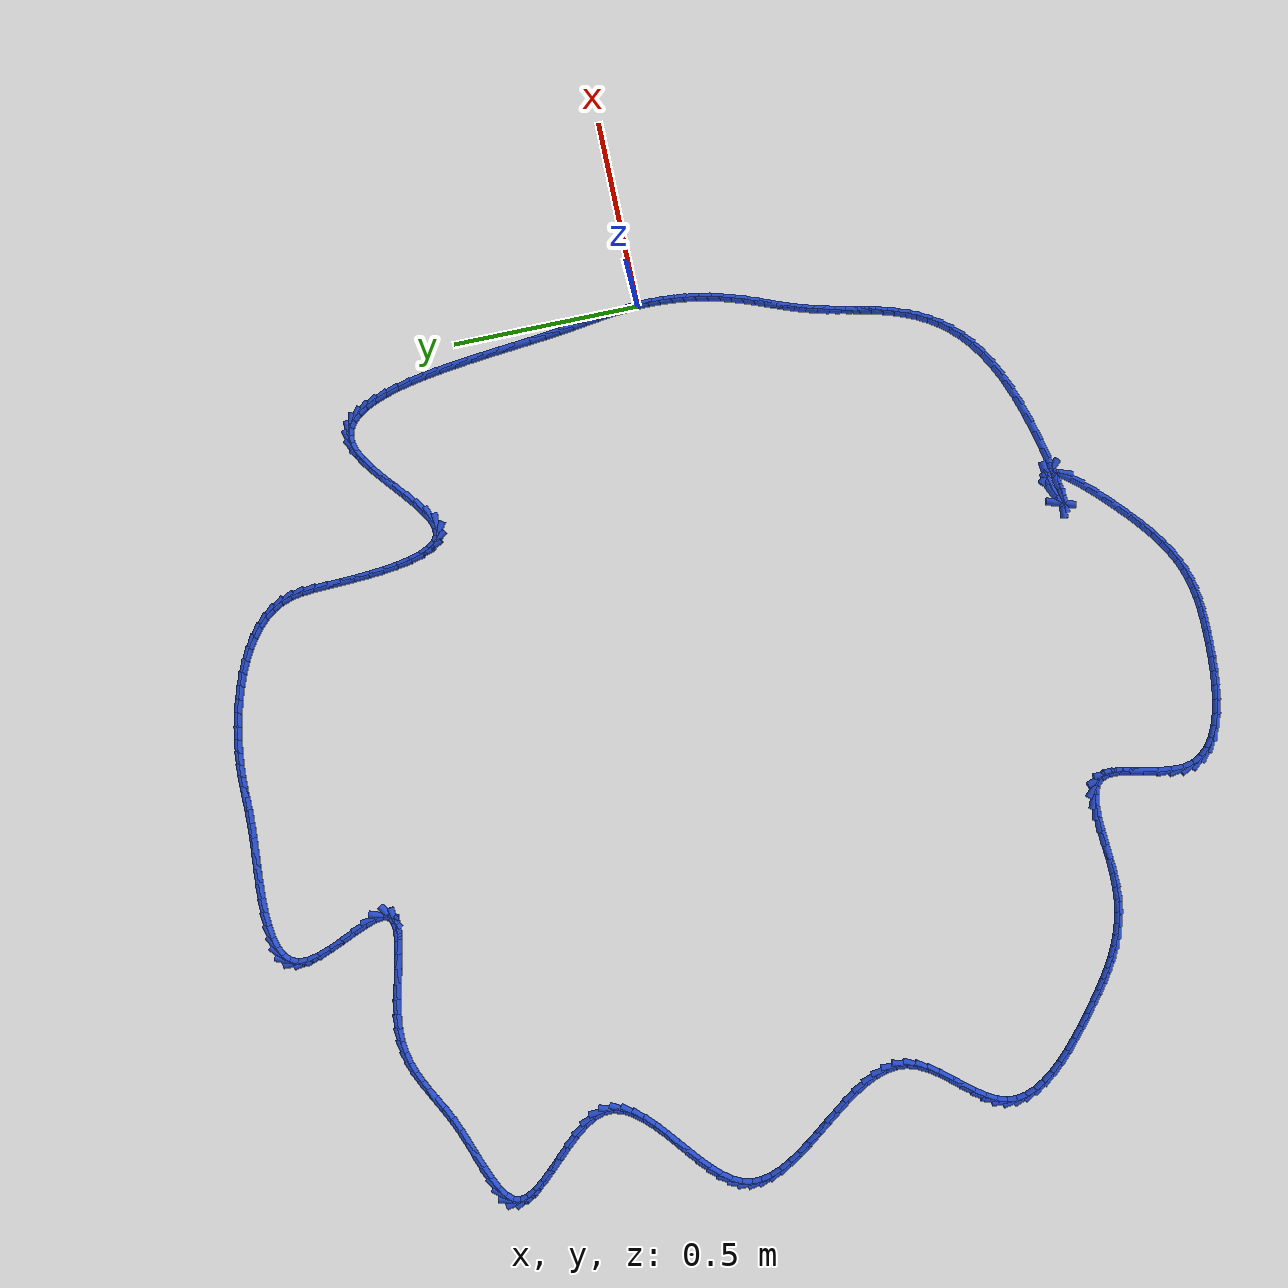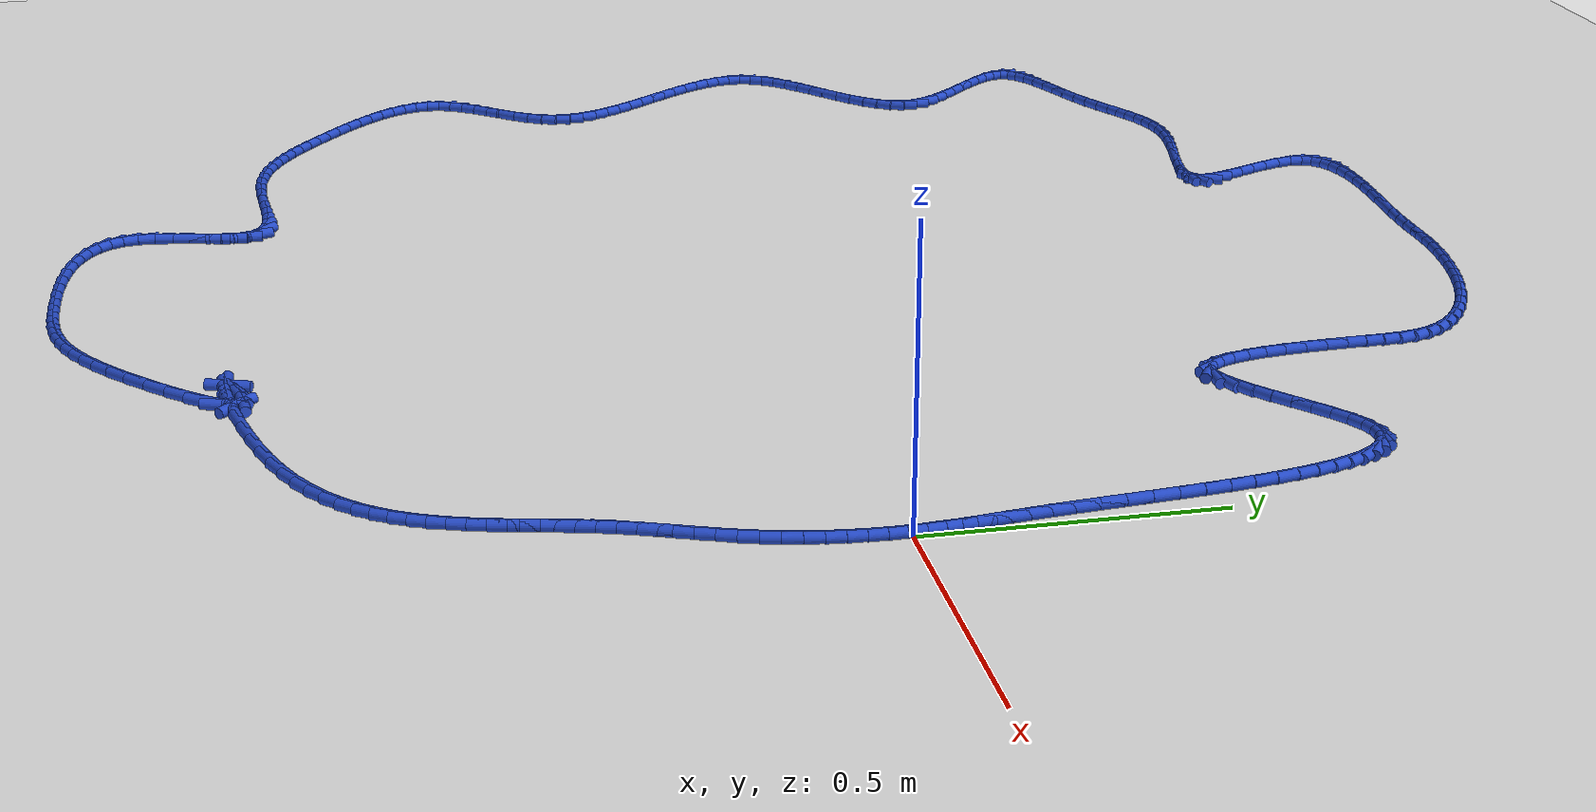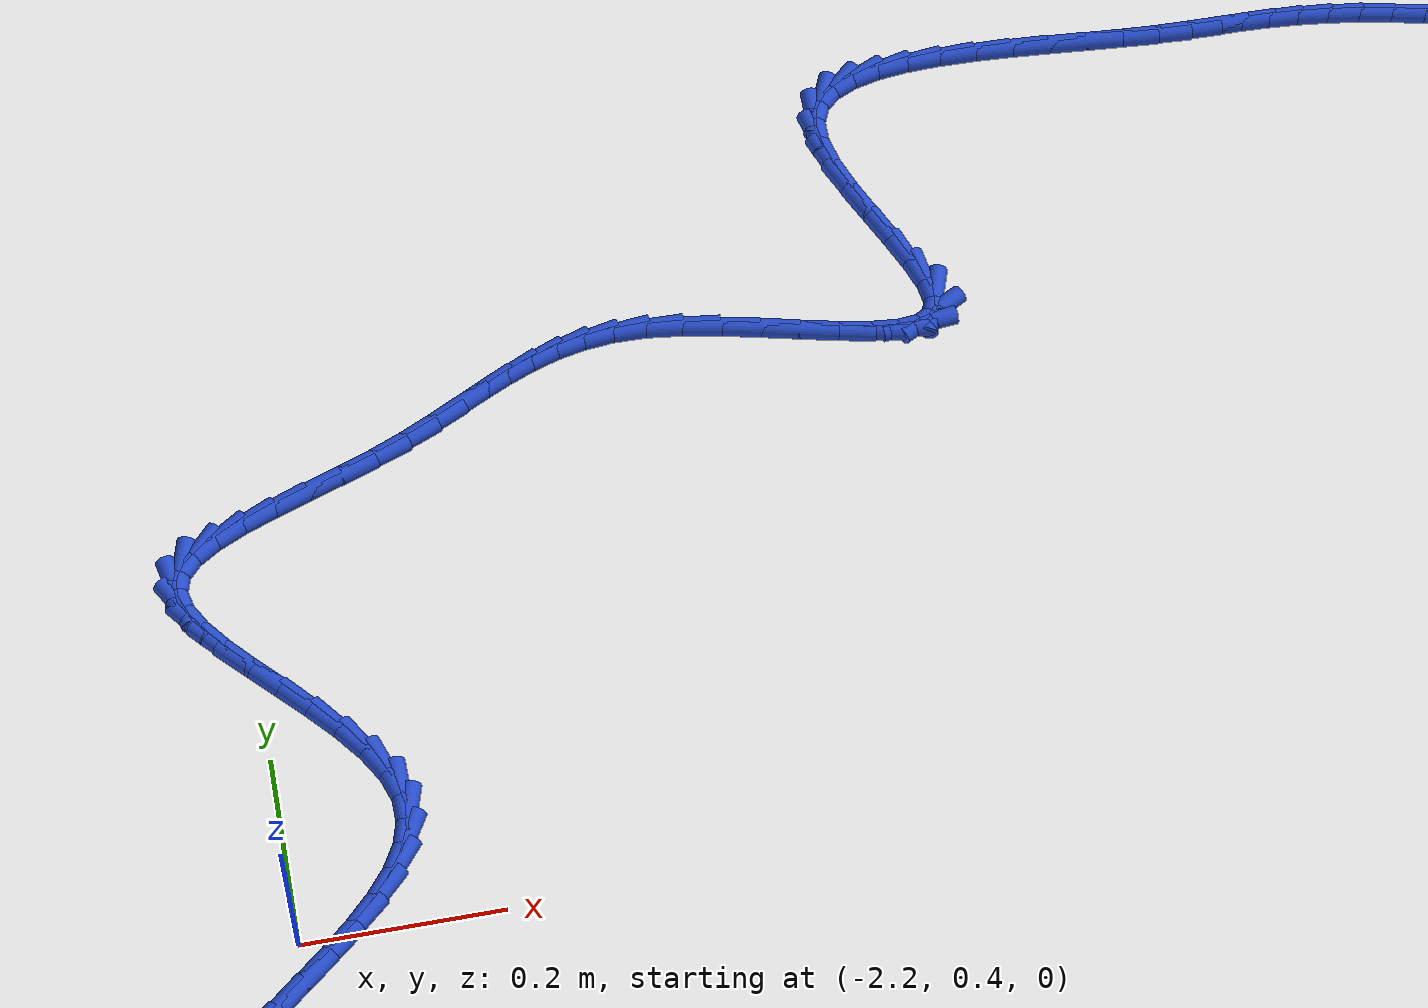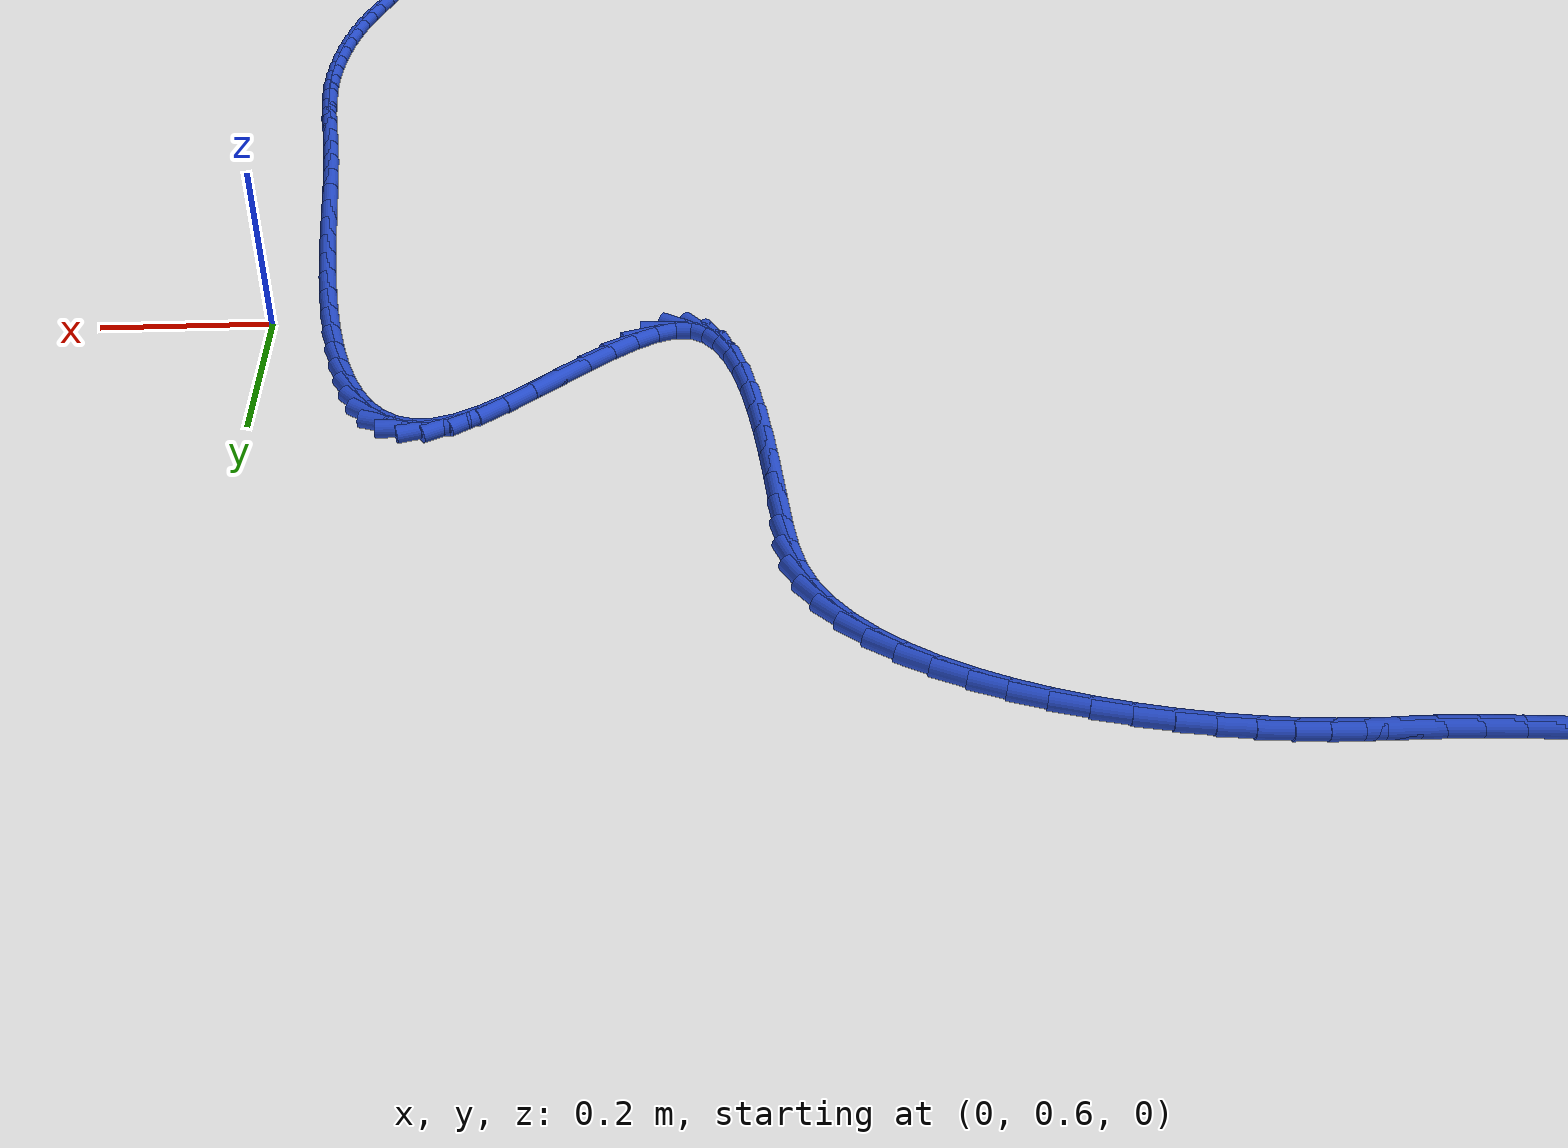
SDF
<sdf version="1.6">
 <world name="default">
  <light name="sun" type="directional">
   <pose>0 0 10 0 -0 0</pose>
   <diffuse>0.8 0.8 0.8 1</diffuse>
   <specular>0.2 0.2 0.2 1</specular>
   <attenuation>
    <range>1000</range>
    <constant>0.9</constant>
    <linear>0.01</linear>
    <quadratic>0.001</quadratic>
   </attenuation>
   <direction>-0.5 0.1 -0.9</direction>
  </light>
  <model name="ground_plane">
   <static>1</static>
   <link name="link">
    <collision name="collision">
     <geometry><plane><normal>0 0 1</normal><size>100 100</size></plane></geometry>
     <surface><friction><ode><mu>100</mu><mu2>50</mu2></ode></friction></surface>
    </collision>
    <visual name="visual">
     <cast_shadows>0</cast_shadows>
     <geometry><plane><normal>0 0 1</normal><size>100 100</size></plane></geometry>
     <material>
      <script><uri>file://media/materials/scripts/gazebo.material</uri><name>Gazebo/WhiteGlow</name></script>
     </material>
    </visual>
   </link>
  </model>
  <gravity>0 0 -9.8</gravity>
  <magnetic_field>6e-06 2.3e-05 -4.2e-05</magnetic_field>
  <atmosphere type="adiabatic"/>
  <physics name="default_physics" default="0" type="ode">
   <max_step_size>0.001</max_step_size>
   <real_time_factor>1</real_time_factor>
   <real_time_update_rate>1000</real_time_update_rate>
  </physics>
  <scene><ambient>0.4 0.4 0.4 1</ambient><background>0.7 0.7 0.7 1</background><shadows>1</shadows></scene>
  <spherical_coordinates>
   <surface_model>EARTH_WGS84</surface_model>
   <latitude_deg>0</latitude_deg>
   <longitude_deg>0</longitude_deg>
   <elevation>0</elevation>
   <heading_deg>0</heading_deg>
  </spherical_coordinates>
  <model name="line">
   <link name="link_0">
    <pose>-6.071532165918825e-18 -3.469446951953614e-17 0.01 0 1.57 -1.5163979464009278</pose>
    <collision name="collision">
     <geometry><cylinder><radius>0.01</radius><length>0.08</length></cylinder></geometry>
    </collision>
    <visual name="visual">
     <material>
      <script><name>Gazebo/Blue</name><uri>file://media/materials/scripts/gazebo.material</uri></script>
     </material>
     <geometry><cylinder><radius>0.01</radius><length>0.08</length></cylinder></geometry>
    </visual>
   </link>
   <link name="link_1">
    <pose>-0.0016290830249006591 0.029917725074173986 0.01 0 1.57 -1.482501930360785</pose>
    <collision name="collision">
     <geometry><cylinder><radius>0.01</radius><length>0.08</length></cylinder></geometry>
    </collision>
    <visual name="visual">
     <material>
      <script><name>Gazebo/Blue</name><uri>file://media/materials/scripts/gazebo.material</uri></script>
     </material>
     <geometry><cylinder><radius>0.01</radius><length>0.08</length></cylinder></geometry>
    </visual>
   </link>
   <link name="link_2">
    <pose>-0.004249189029331303 0.05951522925899522 0.01 0 1.57 -1.4571306769228125</pose>
    <collision name="collision">
     <geometry><cylinder><radius>0.01</radius><length>0.08</length></cylinder></geometry>
    </collision>
    <visual name="visual">
     <material>
      <script><name>Gazebo/Blue</name><uri>file://media/materials/scripts/gazebo.material</uri></script>
     </material>
     <geometry><cylinder><radius>0.01</radius><length>0.08</length></cylinder></geometry>
    </visual>
   </link>
   <link name="link_3">
    <pose>-0.007646788076500758 0.08927755623955241 0.01 0 1.57 -1.441263394326055</pose>
    <collision name="collision">
     <geometry><cylinder><radius>0.01</radius><length>0.08</length></cylinder></geometry>
    </collision>
    <visual name="visual">
     <material>
      <script><name>Gazebo/Blue</name><uri>file://media/materials/scripts/gazebo.material</uri></script>
     </material>
     <geometry><cylinder><radius>0.01</radius><length>0.08</length></cylinder></geometry>
    </visual>
   </link>
   <link name="link_4">
    <pose>-0.011608350229617839 0.1196897497009344 0.01 0 1.57 -1.4349537684915146</pose>
    <collision name="collision">
     <geometry><cylinder><radius>0.01</radius><length>0.08</length></cylinder></geometry>
    </collision>
    <visual name="visual">
     <material>
      <script><name>Gazebo/Blue</name><uri>file://media/materials/scripts/gazebo.material</uri></script>
     </material>
     <geometry><cylinder><radius>0.01</radius><length>0.08</length></cylinder></geometry>
    </visual>
   </link>
   <link name="link_5">
    <pose>-0.01592034555189139 0.15123685332823003 0.01 0 1.57 -1.4374561681270017</pose>
    <collision name="collision">
     <geometry><cylinder><radius>0.01</radius><length>0.08</length></cylinder></geometry>
    </collision>
    <visual name="visual">
     <material>
      <script><name>Gazebo/Blue</name><uri>file://media/materials/scripts/gazebo.material</uri></script>
     </material>
     <geometry><cylinder><radius>0.01</radius><length>0.08</length></cylinder></geometry>
    </visual>
   </link>
   <link name="link_6">
    <pose>-0.020369244106530203 0.18440391080652804 0.01 0 1.57 -1.447466917418745</pose>
    <collision name="collision">
     <geometry><cylinder><radius>0.01</radius><length>0.08</length></cylinder></geometry>
    </collision>
    <visual name="visual">
     <material>
      <script><name>Gazebo/Blue</name><uri>file://media/materials/scripts/gazebo.material</uri></script>
     </material>
     <geometry><cylinder><radius>0.01</radius><length>0.08</length></cylinder></geometry>
    </visual>
   </link>
   <link name="link_7">
    <pose>-0.02474151595674313 0.21967596582091728 0.01 0 1.57 -1.4618403567247256</pose>
    <collision name="collision">
     <geometry><cylinder><radius>0.01</radius><length>0.08</length></cylinder></geometry>
    </collision>
    <visual name="visual">
     <material>
      <script><name>Gazebo/Blue</name><uri>file://media/materials/scripts/gazebo.material</uri></script>
     </material>
     <geometry><cylinder><radius>0.01</radius><length>0.08</length></cylinder></geometry>
    </visual>
   </link>
   <link name="link_8">
    <pose>-0.028869115283309703 0.25740912460940285 0.01 0 1.57 -1.4722458426684462</pose>
    <collision name="collision">
     <geometry><cylinder><radius>0.01</radius><length>0.08</length></cylinder></geometry>
    </collision>
    <visual name="visual">
     <material>
      <script><name>Gazebo/Blue</name><uri>file://media/materials/scripts/gazebo.material</uri></script>
     </material>
     <geometry><cylinder><radius>0.01</radius><length>0.08</length></cylinder></geometry>
    </visual>
   </link>
   <link name="link_9">
    <pose>-0.032813919533488854 0.2973077116323413 0.01 0 1.57 -1.4773231016164692</pose>
    <collision name="collision">
     <geometry><cylinder><radius>0.01</radius><length>0.08</length></cylinder></geometry>
    </collision>
    <visual name="visual">
     <material>
      <script><name>Gazebo/Blue</name><uri>file://media/materials/scripts/gazebo.material</uri></script>
     </material>
     <geometry><cylinder><radius>0.01</radius><length>0.08</length></cylinder></geometry>
    </visual>
   </link>
   <link name="link_10">
    <pose>-0.03671028916036978 0.33887057800625286 0.01 0 1.57 -1.477858585893769</pose>
    <collision name="collision">
     <geometry><cylinder><radius>0.01</radius><length>0.08</length></cylinder></geometry>
    </collision>
    <visual name="visual">
     <material>
      <script><name>Gazebo/Blue</name><uri>file://media/materials/scripts/gazebo.material</uri></script>
     </material>
     <geometry><cylinder><radius>0.01</radius><length>0.08</length></cylinder></geometry>
    </visual>
   </link>
   <link name="link_11">
    <pose>-0.04069261187931073 0.38159649756513436 0.01 0 1.57 -1.4742346559800295</pose>
    <collision name="collision">
     <geometry><cylinder><radius>0.01</radius><length>0.08</length></cylinder></geometry>
    </collision>
    <visual name="visual">
     <material>
      <script><name>Gazebo/Blue</name><uri>file://media/materials/scripts/gazebo.material</uri></script>
     </material>
     <geometry><cylinder><radius>0.01</radius><length>0.08</length></cylinder></geometry>
    </visual>
   </link>
   <link name="link_12">
    <pose>-0.04489527540566993 0.4249842441429827 0.01 0 1.57 -1.4665245592092344</pose>
    <collision name="collision">
     <geometry><cylinder><radius>0.01</radius><length>0.08</length></cylinder></geometry>
    </collision>
    <visual name="visual">
     <material>
      <script><name>Gazebo/Blue</name><uri>file://media/materials/scripts/gazebo.material</uri></script>
     </material>
     <geometry><cylinder><radius>0.01</radius><length>0.08</length></cylinder></geometry>
    </visual>
   </link>
   <link name="link_13">
    <pose>-0.04945266745480564 0.46853259157379484 0.01 0 1.57 -1.454526667403661</pose>
    <collision name="collision">
     <geometry><cylinder><radius>0.01</radius><length>0.08</length></cylinder></geometry>
    </collision>
    <visual name="visual">
     <material>
      <script><name>Gazebo/Blue</name><uri>file://media/materials/scripts/gazebo.material</uri></script>
     </material>
     <geometry><cylinder><radius>0.01</radius><length>0.08</length></cylinder></geometry>
    </visual>
   </link>
   <link name="link_14">
    <pose>-0.05449917574207611 0.5117403136915678 0.01 0 1.57 -1.4377524808276965</pose>
    <collision name="collision">
     <geometry><cylinder><radius>0.01</radius><length>0.08</length></cylinder></geometry>
    </collision>
    <visual name="visual">
     <material>
      <script><name>Gazebo/Blue</name><uri>file://media/materials/scripts/gazebo.material</uri></script>
     </material>
     <geometry><cylinder><radius>0.01</radius><length>0.08</length></cylinder></geometry>
    </visual>
   </link>
   <link name="link_15">
    <pose>-0.06016918798283958 0.5541061843302981 0.01 0 1.57 -1.4153690892996147</pose>
    <collision name="collision">
     <geometry><cylinder><radius>0.01</radius><length>0.08</length></cylinder></geometry>
    </collision>
    <visual name="visual">
     <material>
      <script><name>Gazebo/Blue</name><uri>file://media/materials/scripts/gazebo.material</uri></script>
     </material>
     <geometry><cylinder><radius>0.01</radius><length>0.08</length></cylinder></geometry>
    </visual>
   </link>
   <link name="link_16">
    <pose>-0.06659709189245427 0.595128977323983 0.01 0 1.57 -1.3860842035228762</pose>
    <collision name="collision">
     <geometry><cylinder><radius>0.01</radius><length>0.08</length></cylinder></geometry>
    </collision>
    <visual name="visual">
     <material>
      <script><name>Gazebo/Blue</name><uri>file://media/materials/scripts/gazebo.material</uri></script>
     </material>
     <geometry><cylinder><radius>0.01</radius><length>0.08</length></cylinder></geometry>
    </visual>
   </link>
   <link name="link_17">
    <pose>-0.07391727518627844 0.6343074665066192 0.01 0 1.57 -1.3479465450190615</pose>
    <collision name="collision">
     <geometry><cylinder><radius>0.01</radius><length>0.08</length></cylinder></geometry>
    </collision>
    <visual name="visual">
     <material>
      <script><name>Gazebo/Blue</name><uri>file://media/materials/scripts/gazebo.material</uri></script>
     </material>
     <geometry><cylinder><radius>0.01</radius><length>0.08</length></cylinder></geometry>
    </visual>
   </link>
   <link name="link_18">
    <pose>-0.08226412557967039 0.6711404257122037 0.01 0 1.57 -1.2980122350238568</pose>
    <collision name="collision">
     <geometry><cylinder><radius>0.01</radius><length>0.08</length></cylinder></geometry>
    </collision>
    <visual name="visual">
     <material>
      <script><name>Gazebo/Blue</name><uri>file://media/materials/scripts/gazebo.material</uri></script>
     </material>
     <geometry><cylinder><radius>0.01</radius><length>0.08</length></cylinder></geometry>
    </visual>
   </link>
   <link name="link_19">
    <pose>-0.09177203078798829 0.7051266287747334 0.01 0 1.57 -1.2317980982696835</pose>
    <collision name="collision">
     <geometry><cylinder><radius>0.01</radius><length>0.08</length></cylinder></geometry>
    </collision>
    <visual name="visual">
     <material>
      <script><name>Gazebo/Blue</name><uri>file://media/materials/scripts/gazebo.material</uri></script>
     </material>
     <geometry><cylinder><radius>0.01</radius><length>0.08</length></cylinder></geometry>
    </visual>
   </link>
   <link name="link_20">
    <pose>-0.1025753785265904 0.7357648495282051 0.01 0 1.57 -1.1424267949600215</pose>
    <collision name="collision">
     <geometry><cylinder><radius>0.01</radius><length>0.08</length></cylinder></geometry>
    </collision>
    <visual name="visual">
     <material>
      <script><name>Gazebo/Blue</name><uri>file://media/materials/scripts/gazebo.material</uri></script>
     </material>
     <geometry><cylinder><radius>0.01</radius><length>0.08</length></cylinder></geometry>
    </visual>
   </link>
   <link name="link_21">
    <pose>-0.11480855651083499 0.7625538618066158 0.01 0 1.57 -1.0194956856033608</pose>
    <collision name="collision">
     <geometry><cylinder><radius>0.01</radius><length>0.08</length></cylinder></geometry>
    </collision>
    <visual name="visual">
     <material>
      <script><name>Gazebo/Blue</name><uri>file://media/materials/scripts/gazebo.material</uri></script>
     </material>
     <geometry><cylinder><radius>0.01</radius><length>0.08</length></cylinder></geometry>
    </visual>
   </link>
   <link name="link_22">
    <pose>-0.12860595245608025 0.7849924394439622 0.01 0 1.57 -0.8485164700208907</pose>
    <collision name="collision">
     <geometry><cylinder><radius>0.01</radius><length>0.08</length></cylinder></geometry>
    </collision>
    <visual name="visual">
     <material>
      <script><name>Gazebo/Blue</name><uri>file://media/materials/scripts/gazebo.material</uri></script>
     </material>
     <geometry><cylinder><radius>0.01</radius><length>0.08</length></cylinder></geometry>
    </visual>
   </link>
   <link name="link_23">
    <pose>-0.14410195407768453 0.8025793562742415 0.01 0 1.57 -0.6147322027704885</pose>
    <collision name="collision">
     <geometry><cylinder><radius>0.01</radius><length>0.08</length></cylinder></geometry>
    </collision>
    <visual name="visual">
     <material>
      <script><name>Gazebo/Blue</name><uri>file://media/materials/scripts/gazebo.material</uri></script>
     </material>
     <geometry><cylinder><radius>0.01</radius><length>0.08</length></cylinder></geometry>
    </visual>
   </link>
   <link name="link_24">
    <pose>-0.16143094909100594 0.8148133861314502 0.01 0 1.57 -0.319313523385471</pose>
    <collision name="collision">
     <geometry><cylinder><radius>0.01</radius><length>0.08</length></cylinder></geometry>
    </collision>
    <visual name="visual">
     <material>
      <script><name>Gazebo/Blue</name><uri>file://media/materials/scripts/gazebo.material</uri></script>
     </material>
     <geometry><cylinder><radius>0.01</radius><length>0.08</length></cylinder></geometry>
    </visual>
   </link>
   <link name="link_25">
    <pose>-0.18072732521140283 0.8211933028495857 0.01 0 1.57 -0.0011485763049443863</pose>
    <collision name="collision">
     <geometry><cylinder><radius>0.01</radius><length>0.08</length></cylinder></geometry>
    </collision>
    <visual name="visual">
     <material>
      <script><name>Gazebo/Blue</name><uri>file://media/materials/scripts/gazebo.material</uri></script>
     </material>
     <geometry><cylinder><radius>0.01</radius><length>0.08</length></cylinder></geometry>
    </visual>
   </link>
   <link name="link_26">
    <pose>-0.2021254701542334 0.8212178802626445 0.01 0 1.57 0.2813449475201663</pose>
    <collision name="collision">
     <geometry><cylinder><radius>0.01</radius><length>0.08</length></cylinder></geometry>
    </collision>
    <visual name="visual">
     <material>
      <script><name>Gazebo/Blue</name><uri>file://media/materials/scripts/gazebo.material</uri></script>
     </material>
     <geometry><cylinder><radius>0.01</radius><length>0.08</length></cylinder></geometry>
    </visual>
   </link>
   <link name="link_27">
    <pose>-0.2257592683378419 0.8143874514847792 0.01 0 1.57 0.4851103924217919</pose>
    <collision name="collision">
     <geometry><cylinder><radius>0.01</radius><length>0.08</length></cylinder></geometry>
    </collision>
    <visual name="visual">
     <material>
      <script><name>Gazebo/Blue</name><uri>file://media/materials/scripts/gazebo.material</uri></script>
     </material>
     <geometry><cylinder><radius>0.01</radius><length>0.08</length></cylinder></geometry>
    </visual>
   </link>
   <link name="link_28">
    <pose>-0.25157663554437626 0.8007785048546628 0.01 0 1.57 0.601795979780397</pose>
    <collision name="collision">
     <geometry><cylinder><radius>0.01</radius><length>0.08</length></cylinder></geometry>
    </collision>
    <visual name="visual">
     <material>
      <script><name>Gazebo/Blue</name><uri>file://media/materials/scripts/gazebo.material</uri></script>
     </material>
     <geometry><cylinder><radius>0.01</radius><length>0.08</length></cylinder></geometry>
    </visual>
   </link>
   <link name="link_29">
    <pose>-0.27906252878228 0.7819018357084385 0.01 0 1.57 0.6652639838057579</pose>
    <collision name="collision">
     <geometry><cylinder><radius>0.01</radius><length>0.08</length></cylinder></geometry>
    </collision>
    <visual name="visual">
     <material>
      <script><name>Gazebo/Blue</name><uri>file://media/materials/scripts/gazebo.material</uri></script>
     </material>
     <geometry><cylinder><radius>0.01</radius><length>0.08</length></cylinder></geometry>
    </visual>
   </link>
   <link name="link_30">
    <pose>-0.30763107110891175 0.7594876922525049 0.01 0 1.57 0.6947438430289138</pose>
    <collision name="collision">
     <geometry><cylinder><radius>0.01</radius><length>0.08</length></cylinder></geometry>
    </collision>
    <visual name="visual">
     <material>
      <script><name>Gazebo/Blue</name><uri>file://media/materials/scripts/gazebo.material</uri></script>
     </material>
     <geometry><cylinder><radius>0.01</radius><length>0.08</length></cylinder></geometry>
    </visual>
   </link>
   <link name="link_31">
    <pose>-0.3366963855816303 0.7352663226932604 0.01 0 1.57 0.6978161044609688</pose>
    <collision name="collision">
     <geometry><cylinder><radius>0.01</radius><length>0.08</length></cylinder></geometry>
    </collision>
    <visual name="visual">
     <material>
      <script><name>Gazebo/Blue</name><uri>file://media/materials/scripts/gazebo.material</uri></script>
     </material>
     <geometry><cylinder><radius>0.01</radius><length>0.08</length></cylinder></geometry>
    </visual>
   </link>
   <link name="link_32">
    <pose>-0.36567259525779466 0.710967975237104 0.01 0 1.57 0.674829159289106</pose>
    <collision name="collision">
     <geometry><cylinder><radius>0.01</radius><length>0.08</length></cylinder></geometry>
    </collision>
    <visual name="visual">
     <material>
      <script><name>Gazebo/Blue</name><uri>file://media/materials/scripts/gazebo.material</uri></script>
     </material>
     <geometry><cylinder><radius>0.01</radius><length>0.08</length></cylinder></geometry>
    </visual>
   </link>
   <link name="link_33">
    <pose>-0.39397382319476326 0.6883228980904342 0.01 0 1.57 0.6189506479258206</pose>
    <collision name="collision">
     <geometry><cylinder><radius>0.01</radius><length>0.08</length></cylinder></geometry>
    </collision>
    <visual name="visual">
     <material>
      <script><name>Gazebo/Blue</name><uri>file://media/materials/scripts/gazebo.material</uri></script>
     </material>
     <geometry><cylinder><radius>0.01</radius><length>0.08</length></cylinder></geometry>
    </visual>
   </link>
   <link name="link_34">
    <pose>-0.4210141924498953 0.6690613394596497 0.01 0 1.57 0.5116767681322953</pose>
    <collision name="collision">
     <geometry><cylinder><radius>0.01</radius><length>0.08</length></cylinder></geometry>
    </collision>
    <visual name="visual">
     <material>
      <script><name>Gazebo/Blue</name><uri>file://media/materials/scripts/gazebo.material</uri></script>
     </material>
     <geometry><cylinder><radius>0.01</radius><length>0.08</length></cylinder></geometry>
    </visual>
   </link>
   <link name="link_35">
    <pose>-0.44620782608054943 0.6549135475511496 0.01 0 1.57 0.31050978372341387</pose>
    <collision name="collision">
     <geometry><cylinder><radius>0.01</radius><length>0.08</length></cylinder></geometry>
    </collision>
    <visual name="visual">
     <material>
      <script><name>Gazebo/Blue</name><uri>file://media/materials/scripts/gazebo.material</uri></script>
     </material>
     <geometry><cylinder><radius>0.01</radius><length>0.08</length></cylinder></geometry>
    </visual>
   </link>
   <link name="link_36">
    <pose>-0.46896884714408427 0.647609770571332 0.01 0 1.57 -0.06306543575020025</pose>
    <collision name="collision">
     <geometry><cylinder><radius>0.01</radius><length>0.08</length></cylinder></geometry>
    </collision>
    <visual name="visual">
     <material>
      <script><name>Gazebo/Blue</name><uri>file://media/materials/scripts/gazebo.material</uri></script>
     </material>
     <geometry><cylinder><radius>0.01</radius><length>0.08</length></cylinder></geometry>
    </visual>
   </link>
   <link name="link_37">
    <pose>-0.4887185126162929 0.6488569457109368 0.01 0 1.57 -0.5600312593526471</pose>
    <collision name="collision">
     <geometry><cylinder><radius>0.01</radius><length>0.08</length></cylinder></geometry>
    </collision>
    <visual name="visual">
     <material>
      <script><name>Gazebo/Blue</name><uri>file://media/materials/scripts/gazebo.material</uri></script>
     </material>
     <geometry><cylinder><radius>0.01</radius><length>0.08</length></cylinder></geometry>
    </visual>
   </link>
   <link name="link_38">
    <pose>-0.5052306494924509 0.659209941305267 0.01 0 1.57 -0.934736751435346</pose>
    <collision name="collision">
     <geometry><cylinder><radius>0.01</radius><length>0.08</length></cylinder></geometry>
    </collision>
    <visual name="visual">
     <material>
      <script><name>Gazebo/Blue</name><uri>file://media/materials/scripts/gazebo.material</uri></script>
     </material>
     <geometry><cylinder><radius>0.01</radius><length>0.08</length></cylinder></geometry>
    </visual>
   </link>
   <link name="link_39">
    <pose>-0.5187860987987545 0.6775668907376597 0.01 0 1.57 -1.1609179245999288</pose>
    <collision name="collision">
     <geometry><cylinder><radius>0.01</radius><length>0.08</length></cylinder></geometry>
    </collision>
    <visual name="visual">
     <material>
      <script><name>Gazebo/Blue</name><uri>file://media/materials/scripts/gazebo.material</uri></script>
     </material>
     <geometry><cylinder><radius>0.01</radius><length>0.08</length></cylinder></geometry>
    </visual>
   </link>
   <link name="link_40">
    <pose>-0.52970500794141 0.702697488631128 0.01 0 1.57 -1.2973700963170323</pose>
    <collision name="collision">
     <geometry><cylinder><radius>0.01</radius><length>0.08</length></cylinder></geometry>
    </collision>
    <visual name="visual">
     <material>
      <script><name>Gazebo/Blue</name><uri>file://media/materials/scripts/gazebo.material</uri></script>
     </material>
     <geometry><cylinder><radius>0.01</radius><length>0.08</length></cylinder></geometry>
    </visual>
   </link>
   <link name="link_41">
    <pose>-0.538307524326624 0.7333714296086851 0.01 0 1.57 -1.3841726923106685</pose>
    <collision name="collision">
     <geometry><cylinder><radius>0.01</radius><length>0.08</length></cylinder></geometry>
    </collision>
    <visual name="visual">
     <material>
      <script><name>Gazebo/Blue</name><uri>file://media/materials/scripts/gazebo.material</uri></script>
     </material>
     <geometry><cylinder><radius>0.01</radius><length>0.08</length></cylinder></geometry>
    </visual>
   </link>
   <link name="link_42">
    <pose>-0.5449137953606028 0.7683584082933431 0.01 0 1.57 -1.4420092853491449</pose>
    <collision name="collision">
     <geometry><cylinder><radius>0.01</radius><length>0.08</length></cylinder></geometry>
    </collision>
    <visual name="visual">
     <material>
      <script><name>Gazebo/Blue</name><uri>file://media/materials/scripts/gazebo.material</uri></script>
     </material>
     <geometry><cylinder><radius>0.01</radius><length>0.08</length></cylinder></geometry>
    </visual>
   </link>
   <link name="link_43">
    <pose>-0.5498439684495531 0.8064281193081151 0.01 0 1.57 -1.4815045563050857</pose>
    <collision name="collision">
     <geometry><cylinder><radius>0.01</radius><length>0.08</length></cylinder></geometry>
    </collision>
    <visual name="visual">
     <material>
      <script><name>Gazebo/Blue</name><uri>file://media/materials/scripts/gazebo.material</uri></script>
     </material>
     <geometry><cylinder><radius>0.01</radius><length>0.08</length></cylinder></geometry>
    </visual>
   </link>
   <link name="link_44">
    <pose>-0.5534181909996813 0.8463502572760144 0.01 0 1.57 -1.5082693379018786</pose>
    <collision name="collision">
     <geometry><cylinder><radius>0.01</radius><length>0.08</length></cylinder></geometry>
    </collision>
    <visual name="visual">
     <material>
      <script><name>Gazebo/Blue</name><uri>file://media/materials/scripts/gazebo.material</uri></script>
     </material>
     <geometry><cylinder><radius>0.01</radius><length>0.08</length></cylinder></geometry>
    </visual>
   </link>
   <link name="link_45">
    <pose>-0.5559566104171938 0.8868945168200535 0.01 0 1.57 -1.525185947890008</pose>
    <collision name="collision">
     <geometry><cylinder><radius>0.01</radius><length>0.08</length></cylinder></geometry>
    </collision>
    <visual name="visual">
     <material>
      <script><name>Gazebo/Blue</name><uri>file://media/materials/scripts/gazebo.material</uri></script>
     </material>
     <geometry><cylinder><radius>0.01</radius><length>0.08</length></cylinder></geometry>
    </visual>
   </link>
   <link name="link_46">
    <pose>-0.5577793741082971 0.9268305925632453 0.01 0 1.57 -1.5333506944150765</pose>
    <collision name="collision">
     <geometry><cylinder><radius>0.01</radius><length>0.08</length></cylinder></geometry>
    </collision>
    <visual name="visual">
     <material>
      <script><name>Gazebo/Blue</name><uri>file://media/materials/scripts/gazebo.material</uri></script>
     </material>
     <geometry><cylinder><radius>0.01</radius><length>0.08</length></cylinder></geometry>
    </visual>
   </link>
   <link name="link_47">
    <pose>-0.5592066294791979 0.9649281791286026 0.01 0 1.57 -1.5299484255990445</pose>
    <collision name="collision">
     <geometry><cylinder><radius>0.01</radius><length>0.08</length></cylinder></geometry>
    </collision>
    <visual name="visual">
     <material>
      <script><name>Gazebo/Blue</name><uri>file://media/materials/scripts/gazebo.material</uri></script>
     </material>
     <geometry><cylinder><radius>0.01</radius><length>0.08</length></cylinder></geometry>
    </visual>
   </link>
   <link name="link_48">
    <pose>-0.5606433944602222 1.0000821465259646 0.01 0 1.57 -1.4914541092336222</pose>
    <collision name="collision">
     <geometry><cylinder><radius>0.01</radius><length>0.08</length></cylinder></geometry>
    </collision>
    <visual name="visual">
     <material>
      <script><name>Gazebo/Blue</name><uri>file://media/materials/scripts/gazebo.material</uri></script>
     </material>
     <geometry><cylinder><radius>0.01</radius><length>0.08</length></cylinder></geometry>
    </visual>
   </link>
   <link name="link_49">
    <pose>-0.5631991547111065 1.032226382980859 0.01 0 1.57 -1.3989947967397172</pose>
    <collision name="collision">
     <geometry><cylinder><radius>0.01</radius><length>0.08</length></cylinder></geometry>
    </collision>
    <visual name="visual">
     <material>
      <script><name>Gazebo/Blue</name><uri>file://media/materials/scripts/gazebo.material</uri></script>
     </material>
     <geometry><cylinder><radius>0.01</radius><length>0.08</length></cylinder></geometry>
    </visual>
   </link>
   <link name="link_50">
    <pose>-0.5683321106896472 1.0618090955614503 0.01 0 1.57 -1.2503103855909325</pose>
    <collision name="collision">
     <geometry><cylinder><radius>0.01</radius><length>0.08</length></cylinder></geometry>
    </collision>
    <visual name="visual">
     <material>
      <script><name>Gazebo/Blue</name><uri>file://media/materials/scripts/gazebo.material</uri></script>
     </material>
     <geometry><cylinder><radius>0.01</radius><length>0.08</length></cylinder></geometry>
    </visual>
   </link>
   <link name="link_51">
    <pose>-0.57744703484086 1.0892695755860515 0.01 0 1.57 -1.0839318996817784</pose>
    <collision name="collision">
     <geometry><cylinder><radius>0.01</radius><length>0.08</length></cylinder></geometry>
    </collision>
    <visual name="visual">
     <material>
      <script><name>Gazebo/Blue</name><uri>file://media/materials/scripts/gazebo.material</uri></script>
     </material>
     <geometry><cylinder><radius>0.01</radius><length>0.08</length></cylinder></geometry>
    </visual>
   </link>
   <link name="link_52">
    <pose>-0.5909770361302555 1.1148283958891256 0.01 0 1.57 -0.9331206349444616</pose>
    <collision name="collision">
     <geometry><cylinder><radius>0.01</radius><length>0.08</length></cylinder></geometry>
    </collision>
    <visual name="visual">
     <material>
      <script><name>Gazebo/Blue</name><uri>file://media/materials/scripts/gazebo.material</uri></script>
     </material>
     <geometry><cylinder><radius>0.01</radius><length>0.08</length></cylinder></geometry>
    </visual>
   </link>
   <link name="link_53">
    <pose>-0.6085315673398851 1.1385207268119244 0.01 0 1.57 -0.8014993310196985</pose>
    <collision name="collision">
     <geometry><cylinder><radius>0.01</radius><length>0.08</length></cylinder></geometry>
    </collision>
    <visual name="visual">
     <material>
      <script><name>Gazebo/Blue</name><uri>file://media/materials/scripts/gazebo.material</uri></script>
     </material>
     <geometry><cylinder><radius>0.01</radius><length>0.08</length></cylinder></geometry>
    </visual>
   </link>
   <link name="link_54">
    <pose>-0.6296940193642089 1.1603758722443411 0.01 0 1.57 -0.6887096014754508</pose>
    <collision name="collision">
     <geometry><cylinder><radius>0.01</radius><length>0.08</length></cylinder></geometry>
    </collision>
    <visual name="visual">
     <material>
      <script><name>Gazebo/Blue</name><uri>file://media/materials/scripts/gazebo.material</uri></script>
     </material>
     <geometry><cylinder><radius>0.01</radius><length>0.08</length></cylinder></geometry>
    </visual>
   </link>
   <link name="link_55">
    <pose>-0.6540477830976876 1.180423136076269 0.01 0 1.57 -0.5926592251216902</pose>
    <collision name="collision">
     <geometry><cylinder><radius>0.01</radius><length>0.08</length></cylinder></geometry>
    </collision>
    <visual name="visual">
     <material>
      <script><name>Gazebo/Blue</name><uri>file://media/materials/scripts/gazebo.material</uri></script>
     </material>
     <geometry><cylinder><radius>0.01</radius><length>0.08</length></cylinder></geometry>
    </visual>
   </link>
   <link name="link_56">
    <pose>-0.6811762494347813 1.1986918221976015 0.01 0 1.57 -0.5106674456410758</pose>
    <collision name="collision">
     <geometry><cylinder><radius>0.01</radius><length>0.08</length></cylinder></geometry>
    </collision>
    <visual name="visual">
     <material>
      <script><name>Gazebo/Blue</name><uri>file://media/materials/scripts/gazebo.material</uri></script>
     </material>
     <geometry><cylinder><radius>0.01</radius><length>0.08</length></cylinder></geometry>
    </visual>
   </link>
   <link name="link_57">
    <pose>-0.7106628092699502 1.2152112344982313 0.01 0 1.57 -0.4400971768349035</pose>
    <collision name="collision">
     <geometry><cylinder><radius>0.01</radius><length>0.08</length></cylinder></geometry>
    </collision>
    <visual name="visual">
     <material>
      <script><name>Gazebo/Blue</name><uri>file://media/materials/scripts/gazebo.material</uri></script>
     </material>
     <geometry><cylinder><radius>0.01</radius><length>0.08</length></cylinder></geometry>
    </visual>
   </link>
   <link name="link_58">
    <pose>-0.7420908534976549 1.2300106768680519 0.01 0 1.57 -0.37861113742076613</pose>
    <collision name="collision">
     <geometry><cylinder><radius>0.01</radius><length>0.08</length></cylinder></geometry>
    </collision>
    <visual name="visual">
     <material>
      <script><name>Gazebo/Blue</name><uri>file://media/materials/scripts/gazebo.material</uri></script>
     </material>
     <geometry><cylinder><radius>0.01</radius><length>0.08</length></cylinder></geometry>
    </visual>
   </link>
   <link name="link_59">
    <pose>-0.7750437730123558 1.243119453196956 0.01 0 1.57 -0.3242239668933238</pose>
    <collision name="collision">
     <geometry><cylinder><radius>0.01</radius><length>0.08</length></cylinder></geometry>
    </collision>
    <visual name="visual">
     <material>
      <script><name>Gazebo/Blue</name><uri>file://media/materials/scripts/gazebo.material</uri></script>
     </material>
     <geometry><cylinder><radius>0.01</radius><length>0.08</length></cylinder></geometry>
    </visual>
   </link>
   <link name="link_60">
    <pose>-0.809104958708513 1.2545668673748376 0.01 0 1.57 -0.2752635623198393</pose>
    <collision name="collision">
     <geometry><cylinder><radius>0.01</radius><length>0.08</length></cylinder></geometry>
    </collision>
    <visual name="visual">
     <material>
      <script><name>Gazebo/Blue</name><uri>file://media/materials/scripts/gazebo.material</uri></script>
     </material>
     <geometry><cylinder><radius>0.01</radius><length>0.08</length></cylinder></geometry>
    </visual>
   </link>
   <link name="link_61">
    <pose>-0.8438578014805871 1.2643822232915887 0.01 0 1.57 -0.2302991390069512</pose>
    <collision name="collision">
     <geometry><cylinder><radius>0.01</radius><length>0.08</length></cylinder></geometry>
    </collision>
    <visual name="visual">
     <material>
      <script><name>Gazebo/Blue</name><uri>file://media/materials/scripts/gazebo.material</uri></script>
     </material>
     <geometry><cylinder><radius>0.01</radius><length>0.08</length></cylinder></geometry>
    </visual>
   </link>
   <link name="link_62">
    <pose>-0.8788856922230381 1.2725948248371037 0.01 0 1.57 -0.18805929373507083</pose>
    <collision name="collision">
     <geometry><cylinder><radius>0.01</radius><length>0.08</length></cylinder></geometry>
    </collision>
    <visual name="visual">
     <material>
      <script><name>Gazebo/Blue</name><uri>file://media/materials/scripts/gazebo.material</uri></script>
     </material>
     <geometry><cylinder><radius>0.01</radius><length>0.08</length></cylinder></geometry>
    </visual>
   </link>
   <link name="link_63">
    <pose>-0.9137720218303266 1.2792339759012747 0.01 0 1.57 -0.1473449015706178</pose>
    <collision name="collision">
     <geometry><cylinder><radius>0.01</radius><length>0.08</length></cylinder></geometry>
    </collision>
    <visual name="visual">
     <material>
      <script><name>Gazebo/Blue</name><uri>file://media/materials/scripts/gazebo.material</uri></script>
     </material>
     <geometry><cylinder><radius>0.01</radius><length>0.08</length></cylinder></geometry>
    </visual>
   </link>
   <link name="link_64">
    <pose>-0.9481001811969129 1.284328980373996 0.01 0 1.57 -0.10693086921144568</pose>
    <collision name="collision">
     <geometry><cylinder><radius>0.01</radius><length>0.08</length></cylinder></geometry>
    </collision>
    <visual name="visual">
     <material>
      <script><name>Gazebo/Blue</name><uri>file://media/materials/scripts/gazebo.material</uri></script>
     </material>
     <geometry><cylinder><radius>0.01</radius><length>0.08</length></cylinder></geometry>
    </visual>
   </link>
   <link name="link_65">
    <pose>-0.981453561217257 1.2879091421451596 0.01 0 1.57 -0.06549317366335013</pose>
    <collision name="collision">
     <geometry><cylinder><radius>0.01</radius><length>0.08</length></cylinder></geometry>
    </collision>
    <visual name="visual">
     <material>
      <script><name>Gazebo/Blue</name><uri>file://media/materials/scripts/gazebo.material</uri></script>
     </material>
     <geometry><cylinder><radius>0.01</radius><length>0.08</length></cylinder></geometry>
    </visual>
   </link>
   <link name="link_66">
    <pose>-1.0134207095680028 1.2900057707298467 0.01 0 1.57 -0.02750333178696695</pose>
    <collision name="collision">
     <geometry><cylinder><radius>0.01</radius><length>0.08</length></cylinder></geometry>
    </collision>
    <visual name="visual">
     <material>
      <script><name>Gazebo/Blue</name><uri>file://media/materials/scripts/gazebo.material</uri></script>
     </material>
     <geometry><cylinder><radius>0.01</radius><length>0.08</length></cylinder></geometry>
    </visual>
   </link>
   <link name="link_67">
    <pose>-1.0441036084489705 1.2908498655224814 0.01 0 1.57 -0.0062141048390428645</pose>
    <collision name="collision">
     <geometry><cylinder><radius>0.01</radius><length>0.08</length></cylinder></geometry>
    </collision>
    <visual name="visual">
     <material>
      <script><name>Gazebo/Blue</name><uri>file://media/materials/scripts/gazebo.material</uri></script>
     </material>
     <geometry><cylinder><radius>0.01</radius><length>0.08</length></cylinder></geometry>
    </visual>
   </link>
   <link name="link_68">
    <pose>-1.0745468777904277 1.2910390456248881 0.01 0 1.57 -0.0054606861997451885</pose>
    <collision name="collision">
     <geometry><cylinder><radius>0.01</radius><length>0.08</length></cylinder></geometry>
    </collision>
    <visual name="visual">
     <material>
      <script><name>Gazebo/Blue</name><uri>file://media/materials/scripts/gazebo.material</uri></script>
     </material>
     <geometry><cylinder><radius>0.01</radius><length>0.08</length></cylinder></geometry>
    </visual>
   </link>
   <link name="link_69">
    <pose>-1.1058961995063756 1.2912102361349391 0.01 0 1.57 -0.023651308566772233</pose>
    <collision name="collision">
     <geometry><cylinder><radius>0.01</radius><length>0.08</length></cylinder></geometry>
    </collision>
    <visual name="visual">
     <material>
      <script><name>Gazebo/Blue</name><uri>file://media/materials/scripts/gazebo.material</uri></script>
     </material>
     <geometry><cylinder><radius>0.01</radius><length>0.08</length></cylinder></geometry>
    </visual>
   </link>
   <link name="link_70">
    <pose>-1.1392972555108176 1.2920003621505056 0.01 0 1.57 -0.05329321475483819</pose>
    <collision name="collision">
     <geometry><cylinder><radius>0.01</radius><length>0.08</length></cylinder></geometry>
    </collision>
    <visual name="visual">
     <material>
      <script><name>Gazebo/Blue</name><uri>file://media/materials/scripts/gazebo.material</uri></script>
     </material>
     <geometry><cylinder><radius>0.01</radius><length>0.08</length></cylinder></geometry>
    </visual>
   </link>
   <link name="link_71">
    <pose>-1.1757144748370885 1.2939429923203563 0.01 0 1.57 -0.07293361830226928</pose>
    <collision name="collision">
     <geometry><cylinder><radius>0.01</radius><length>0.08</length></cylinder></geometry>
    </collision>
    <visual name="visual">
     <material>
      <script><name>Gazebo/Blue</name><uri>file://media/materials/scripts/gazebo.material</uri></script>
     </material>
     <geometry><cylinder><radius>0.01</radius><length>0.08</length></cylinder></geometry>
    </visual>
   </link>
   <link name="link_72">
    <pose>-1.2147503604570982 1.2967950795444112 0.01 0 1.57 -0.07773520650017757</pose>
    <collision name="collision">
     <geometry><cylinder><radius>0.01</radius><length>0.08</length></cylinder></geometry>
    </collision>
    <visual name="visual">
     <material>
      <script><name>Gazebo/Blue</name><uri>file://media/materials/scripts/gazebo.material</uri></script>
     </material>
     <geometry><cylinder><radius>0.01</radius><length>0.08</length></cylinder></geometry>
    </visual>
   </link>
   <link name="link_73">
    <pose>-1.255388137803182 1.2999604439764285 0.01 0 1.57 -0.06977254398684012</pose>
    <collision name="collision">
     <geometry><cylinder><radius>0.01</radius><length>0.08</length></cylinder></geometry>
    </collision>
    <visual name="visual">
     <material>
      <script><name>Gazebo/Blue</name><uri>file://media/materials/scripts/gazebo.material</uri></script>
     </material>
     <geometry><cylinder><radius>0.01</radius><length>0.08</length></cylinder></geometry>
    </visual>
   </link>
   <link name="link_74">
    <pose>-1.2966079162502422 1.3028411288900956 0.01 0 1.57 -0.04895438484107478</pose>
    <collision name="collision">
     <geometry><cylinder><radius>0.01</radius><length>0.08</length></cylinder></geometry>
    </collision>
    <visual name="visual">
     <material>
      <script><name>Gazebo/Blue</name><uri>file://media/materials/scripts/gazebo.material</uri></script>
     </material>
     <geometry><cylinder><radius>0.01</radius><length>0.08</length></cylinder></geometry>
    </visual>
   </link>
   <link name="link_75">
    <pose>-1.3373898051731816 1.3048391775590995 0.01 0 1.57 -0.01315797995251754</pose>
    <collision name="collision">
     <geometry><cylinder><radius>0.01</radius><length>0.08</length></cylinder></geometry>
    </collision>
    <visual name="visual">
     <material>
      <script><name>Gazebo/Blue</name><uri>file://media/materials/scripts/gazebo.material</uri></script>
     </material>
     <geometry><cylinder><radius>0.01</radius><length>0.08</length></cylinder></geometry>
    </visual>
   </link>
   <link name="link_76">
    <pose>-1.3767139139469038 1.305356633257128 0.01 0 1.57 0.04234224604674094</pose>
    <collision name="collision">
     <geometry><cylinder><radius>0.01</radius><length>0.08</length></cylinder></geometry>
    </collision>
    <visual name="visual">
     <material>
      <script><name>Gazebo/Blue</name><uri>file://media/materials/scripts/gazebo.material</uri></script>
     </material>
     <geometry><cylinder><radius>0.01</radius><length>0.08</length></cylinder></geometry>
    </visual>
   </link>
   <link name="link_77">
    <pose>-1.413560351946312 1.3037955392578684 0.01 0 1.57 0.12639140691439146</pose>
    <collision name="collision">
     <geometry><cylinder><radius>0.01</radius><length>0.08</length></cylinder></geometry>
    </collision>
    <visual name="visual">
     <material>
      <script><name>Gazebo/Blue</name><uri>file://media/materials/scripts/gazebo.material</uri></script>
     </material>
     <geometry><cylinder><radius>0.01</radius><length>0.08</length></cylinder></geometry>
    </visual>
   </link>
   <link name="link_78">
    <pose>-1.4469092285463092 1.2995579388350074 0.01 0 1.57 0.25488432973484554</pose>
    <collision name="collision">
     <geometry><cylinder><radius>0.01</radius><length>0.08</length></cylinder></geometry>
    </collision>
    <visual name="visual">
     <material>
      <script><name>Gazebo/Blue</name><uri>file://media/materials/scripts/gazebo.material</uri></script>
     </material>
     <geometry><cylinder><radius>0.01</radius><length>0.08</length></cylinder></geometry>
    </visual>
   </link>
   <link name="link_79">
    <pose>-1.4757406531217967 1.2920458752622328 0.01 0 1.57 0.454589877610765</pose>
    <collision name="collision">
     <geometry><cylinder><radius>0.01</radius><length>0.08</length></cylinder></geometry>
    </collision>
    <visual name="visual">
     <material>
      <script><name>Gazebo/Blue</name><uri>file://media/materials/scripts/gazebo.material</uri></script>
     </material>
     <geometry><cylinder><radius>0.01</radius><length>0.08</length></cylinder></geometry>
    </visual>
   </link>
   <link name="link_80">
    <pose>-1.499034735047679 1.2806613918132324 0.01 0 1.57 0.7583430188637666</pose>
    <collision name="collision">
     <geometry><cylinder><radius>0.01</radius><length>0.08</length></cylinder></geometry>
    </collision>
    <visual name="visual">
     <material>
      <script><name>Gazebo/Blue</name><uri>file://media/materials/scripts/gazebo.material</uri></script>
     </material>
     <geometry><cylinder><radius>0.01</radius><length>0.08</length></cylinder></geometry>
    </visual>
   </link>
   <link name="link_81">
    <pose>-1.515771583698859 1.2648065317616932 0.01 0 1.57 1.1581521301465278</pose>
    <collision name="collision">
     <geometry><cylinder><radius>0.01</radius><length>0.08</length></cylinder></geometry>
    </collision>
    <visual name="visual">
     <material>
      <script><name>Gazebo/Blue</name><uri>file://media/materials/scripts/gazebo.material</uri></script>
     </material>
     <geometry><cylinder><radius>0.01</radius><length>0.08</length></cylinder></geometry>
    </visual>
   </link>
   <link name="link_82">
    <pose>-1.5249313084502394 1.243883338381302 0.01 0 1.57 1.5434661027120598</pose>
    <collision name="collision">
     <geometry><cylinder><radius>0.01</radius><length>0.08</length></cylinder></geometry>
    </collision>
    <visual name="visual">
     <material>
      <script><name>Gazebo/Blue</name><uri>file://media/materials/scripts/gazebo.material</uri></script>
     </material>
     <geometry><cylinder><radius>0.01</radius><length>0.08</length></cylinder></geometry>
    </visual>
   </link>
   <link name="link_83">
    <pose>-1.5256550989267372 1.2174067805711528 0.01 0 1.57 -1.3600200276536794</pose>
    <collision name="collision">
     <geometry><cylinder><radius>0.01</radius><length>0.08</length></cylinder></geometry>
    </collision>
    <visual name="visual">
     <material>
      <script><name>Gazebo/Blue</name><uri>file://media/materials/scripts/gazebo.material</uri></script>
     </material>
     <geometry><cylinder><radius>0.01</radius><length>0.08</length></cylinder></geometry>
    </visual>
   </link>
   <link name="link_84">
    <pose>-1.5189832409724269 1.1862231923619113 0.01 0 1.57 -1.2386243153492944</pose>
    <collision name="collision">
     <geometry><cylinder><radius>0.01</radius><length>0.08</length></cylinder></geometry>
    </collision>
    <visual name="visual">
     <material>
      <script><name>Gazebo/Blue</name><uri>file://media/materials/scripts/gazebo.material</uri></script>
     </material>
     <geometry><cylinder><radius>0.01</radius><length>0.08</length></cylinder></geometry>
    </visual>
   </link>
   <link name="link_85">
    <pose>-1.5071939640866625 1.1520467706133433 0.01 0 1.57 -1.179845868983129</pose>
    <collision name="collision">
     <geometry><cylinder><radius>0.01</radius><length>0.08</length></cylinder></geometry>
    </collision>
    <visual name="visual">
     <material>
      <script><name>Gazebo/Blue</name><uri>file://media/materials/scripts/gazebo.material</uri></script>
     </material>
     <geometry><cylinder><radius>0.01</radius><length>0.08</length></cylinder></geometry>
    </visual>
   </link>
   <link name="link_86">
    <pose>-1.4925867092561826 1.1166065825400753 0.01 0 1.57 -1.16261070078067</pose>
    <collision name="collision">
     <geometry><cylinder><radius>0.01</radius><length>0.08</length></cylinder></geometry>
    </collision>
    <visual name="visual">
     <material>
      <script><name>Gazebo/Blue</name><uri>file://media/materials/scripts/gazebo.material</uri></script>
     </material>
     <geometry><cylinder><radius>0.01</radius><length>0.08</length></cylinder></geometry>
    </visual>
   </link>
   <link name="link_87">
    <pose>-1.4774609174677245 1.0816316953567322 0.01 0 1.57 -1.1841858953278552</pose>
    <collision name="collision">
     <geometry><cylinder><radius>0.01</radius><length>0.08</length></cylinder></geometry>
    </collision>
    <visual name="visual">
     <material>
      <script><name>Gazebo/Blue</name><uri>file://media/materials/scripts/gazebo.material</uri></script>
     </material>
     <geometry><cylinder><radius>0.01</radius><length>0.08</length></cylinder></geometry>
    </visual>
   </link>
   <link name="link_88">
    <pose>-1.4641160297080256 1.0488511762779409 0.01 0 1.57 -1.2601419592809815</pose>
    <collision name="collision">
     <geometry><cylinder><radius>0.01</radius><length>0.08</length></cylinder></geometry>
    </collision>
    <visual name="visual">
     <material>
      <script><name>Gazebo/Blue</name><uri>file://media/materials/scripts/gazebo.material</uri></script>
     </material>
     <geometry><cylinder><radius>0.01</radius><length>0.08</length></cylinder></geometry>
    </visual>
   </link>
   <link name="link_89">
    <pose>-1.4548514869638234 1.0199940925183257 0.01 0 1.57 -1.4471124882371735</pose>
    <collision name="collision">
     <geometry><cylinder><radius>0.01</radius><length>0.08</length></cylinder></geometry>
    </collision>
    <visual name="visual">
     <material>
      <script><name>Gazebo/Blue</name><uri>file://media/materials/scripts/gazebo.material</uri></script>
     </material>
     <geometry><cylinder><radius>0.01</radius><length>0.08</length></cylinder></geometry>
    </visual>
   </link>
   <link name="link_90">
    <pose>-1.4519667302218549 0.9967895112925125 0.01 0 1.57 1.225573483149632</pose>
    <collision name="collision">
     <geometry><cylinder><radius>0.01</radius><length>0.08</length></cylinder></geometry>
    </collision>
    <visual name="visual">
     <material>
      <script><name>Gazebo/Blue</name><uri>file://media/materials/scripts/gazebo.material</uri></script>
     </material>
     <geometry><cylinder><radius>0.01</radius><length>0.08</length></cylinder></geometry>
    </visual>
   </link>
   <link name="link_91">
    <pose>-1.4576809671862658 0.9809000433505993 0.01 0 1.57 0.5170347029312008</pose>
    <collision name="collision">
     <geometry><cylinder><radius>0.01</radius><length>0.08</length></cylinder></geometry>
    </collision>
    <visual name="visual">
     <material>
      <script><name>Gazebo/Blue</name><uri>file://media/materials/scripts/gazebo.material</uri></script>
     </material>
     <geometry><cylinder><radius>0.01</radius><length>0.08</length></cylinder></geometry>
    </visual>
   </link>
   <link name="link_92">
    <pose>-1.4724315485109156 0.9725124042028388 0.01 0 1.57 0.09520201269867072</pose>
    <collision name="collision">
     <geometry><cylinder><radius>0.01</radius><length>0.08</length></cylinder></geometry>
    </collision>
    <visual name="visual">
     <material>
      <script><name>Gazebo/Blue</name><uri>file://media/materials/scripts/gazebo.material</uri></script>
     </material>
     <geometry><cylinder><radius>0.01</radius><length>0.08</length></cylinder></geometry>
    </visual>
   </link>
   <link name="link_93">
    <pose>-1.4949085520183283 0.9703660598991153 0.01 0 1.57 -0.09594571729624421</pose>
    <collision name="collision">
     <geometry><cylinder><radius>0.01</radius><length>0.08</length></cylinder></geometry>
    </collision>
    <visual name="visual">
     <material>
      <script><name>Gazebo/Blue</name><uri>file://media/materials/scripts/gazebo.material</uri></script>
     </material>
     <geometry><cylinder><radius>0.01</radius><length>0.08</length></cylinder></geometry>
    </visual>
   </link>
   <link name="link_94">
    <pose>-1.5237287399252064 0.9731397498706305 0.01 0 1.57 -0.18645412499702016</pose>
    <collision name="collision">
     <geometry><cylinder><radius>0.01</radius><length>0.08</length></cylinder></geometry>
    </collision>
    <visual name="visual">
     <material>
      <script><name>Gazebo/Blue</name><uri>file://media/materials/scripts/gazebo.material</uri></script>
     </material>
     <geometry><cylinder><radius>0.01</radius><length>0.08</length></cylinder></geometry>
    </visual>
   </link>
   <link name="link_95">
    <pose>-1.5575088744482528 0.9795122135485858 0.01 0 1.57 -0.2275400065699741</pose>
    <collision name="collision">
     <geometry><cylinder><radius>0.01</radius><length>0.08</length></cylinder></geometry>
    </collision>
    <visual name="visual">
     <material>
      <script><name>Gazebo/Blue</name><uri>file://media/materials/scripts/gazebo.material</uri></script>
     </material>
     <geometry><cylinder><radius>0.01</radius><length>0.08</length></cylinder></geometry>
    </visual>
   </link>
   <link name="link_96">
    <pose>-1.5948657178041665 0.9881621903641817 0.01 0 1.57 -0.23827228776778817</pose>
    <collision name="collision">
     <geometry><cylinder><radius>0.01</radius><length>0.08</length></cylinder></geometry>
    </collision>
    <visual name="visual">
     <material>
      <script><name>Gazebo/Blue</name><uri>file://media/materials/scripts/gazebo.material</uri></script>
     </material>
     <geometry><cylinder><radius>0.01</radius><length>0.08</length></cylinder></geometry>
    </visual>
   </link>
   <link name="link_97">
    <pose>-1.634416032209652 0.9977684197486206 0.01 0 1.57 -0.22508678138082222</pose>
    <collision name="collision">
     <geometry><cylinder><radius>0.01</radius><length>0.08</length></cylinder></geometry>
    </collision>
    <visual name="visual">
     <material>
      <script><name>Gazebo/Blue</name><uri>file://media/materials/scripts/gazebo.material</uri></script>
     </material>
     <geometry><cylinder><radius>0.01</radius><length>0.08</length></cylinder></geometry>
    </visual>
   </link>
   <link name="link_98">
    <pose>-1.6747765798814092 1.007009641133103 0.01 0 1.57 -0.18764840830807814</pose>
    <collision name="collision">
     <geometry><cylinder><radius>0.01</radius><length>0.08</length></cylinder></geometry>
    </collision>
    <visual name="visual">
     <material>
      <script><name>Gazebo/Blue</name><uri>file://media/materials/scripts/gazebo.material</uri></script>
     </material>
     <geometry><cylinder><radius>0.01</radius><length>0.08</length></cylinder></geometry>
    </visual>
   </link>
   <link name="link_99">
    <pose>-1.7145641230361404 1.014564593948831 0.01 0 1.57 -0.1196287221775573</pose>
    <collision name="collision">
     <geometry><cylinder><radius>0.01</radius><length>0.08</length></cylinder></geometry>
    </collision>
    <visual name="visual">
     <material>
      <script><name>Gazebo/Blue</name><uri>file://media/materials/scripts/gazebo.material</uri></script>
     </material>
     <geometry><cylinder><radius>0.01</radius><length>0.08</length></cylinder></geometry>
    </visual>
   </link>
   <link name="link_100">
    <pose>-1.7523954238905484 1.0191120176270052 0.01 0 1.57 -0.013289082040959339</pose>
    <collision name="collision">
     <geometry><cylinder><radius>0.01</radius><length>0.08</length></cylinder></geometry>
    </collision>
    <visual name="visual">
     <material>
      <script><name>Gazebo/Blue</name><uri>file://media/materials/scripts/gazebo.material</uri></script>
     </material>
     <geometry><cylinder><radius>0.01</radius><length>0.08</length></cylinder></geometry>
    </visual>
   </link>
   <link name="link_101">
    <pose>-1.7871519560728155 1.0195739272259872 0.01 0 1.57 0.10790826556473448</pose>
    <collision name="collision">
     <geometry><cylinder><radius>0.01</radius><length>0.08</length></cylinder></geometry>
    </collision>
    <visual name="visual">
     <material>
      <script><name>Gazebo/Blue</name><uri>file://media/materials/scripts/gazebo.material</uri></script>
     </material>
     <geometry><cylinder><radius>0.01</radius><length>0.08</length></cylinder></geometry>
    </visual>
   </link>
   <link name="link_102">
    <pose>-1.8190688712536627 1.016116397789788 0.01 0 1.57 0.22521080983518865</pose>
    <collision name="collision">
     <geometry><cylinder><radius>0.01</radius><length>0.08</length></cylinder></geometry>
    </collision>
    <visual name="visual">
     <material>
      <script><name>Gazebo/Blue</name><uri>file://media/materials/scripts/gazebo.material</uri></script>
     </material>
     <geometry><cylinder><radius>0.01</radius><length>0.08</length></cylinder></geometry>
    </visual>
   </link>
   <link name="link_103">
    <pose>-1.8488128897158085 1.0093021254380234 0.01 0 1.57 0.3279676586462446</pose>
    <collision name="collision">
     <geometry><cylinder><radius>0.01</radius><length>0.08</length></cylinder></geometry>
    </collision>
    <visual name="visual">
     <material>
      <script><name>Gazebo/Blue</name><uri>file://media/materials/scripts/gazebo.material</uri></script>
     </material>
     <geometry><cylinder><radius>0.01</radius><length>0.08</length></cylinder></geometry>
    </visual>
   </link>
   <link name="link_104">
    <pose>-1.877050917183874 0.9996939767155072 0.01 0 1.57 0.4078713341601084</pose>
    <collision name="collision">
     <geometry><cylinder><radius>0.01</radius><length>0.08</length></cylinder></geometry>
    </collision>
    <visual name="visual">
     <material>
      <script><name>Gazebo/Blue</name><uri>file://media/materials/scripts/gazebo.material</uri></script>
     </material>
     <geometry><cylinder><radius>0.01</radius><length>0.08</length></cylinder></geometry>
    </visual>
   </link>
   <link name="link_105">
    <pose>-1.9044498593824788 0.9878548181670527 0.01 0 1.57 0.46052583555647414</pose>
    <collision name="collision">
     <geometry><cylinder><radius>0.01</radius><length>0.08</length></cylinder></geometry>
    </collision>
    <visual name="visual">
     <material>
      <script><name>Gazebo/Blue</name><uri>file://media/materials/scripts/gazebo.material</uri></script>
     </material>
     <geometry><cylinder><radius>0.01</radius><length>0.08</length></cylinder></geometry>
    </visual>
   </link>
   <link name="link_106">
    <pose>-1.9316766220362447 0.9743475163374739 0.01 0 1.57 0.48510825436830396</pose>
    <collision name="collision">
     <geometry><cylinder><radius>0.01</radius><length>0.08</length></cylinder></geometry>
    </collision>
    <visual name="visual">
     <material>
      <script><name>Gazebo/Blue</name><uri>file://media/materials/scripts/gazebo.material</uri></script>
     </material>
     <geometry><cylinder><radius>0.01</radius><length>0.08</length></cylinder></geometry>
    </visual>
   </link>
   <link name="link_107">
    <pose>-1.9593981108697909 0.9597349377715843 0.01 0 1.57 0.48321220923117686</pose>
    <collision name="collision">
     <geometry><cylinder><radius>0.01</radius><length>0.08</length></cylinder></geometry>
    </collision>
    <visual name="visual">
     <material>
      <script><name>Gazebo/Blue</name><uri>file://media/materials/scripts/gazebo.material</uri></script>
     </material>
     <geometry><cylinder><radius>0.01</radius><length>0.08</length></cylinder></geometry>
    </visual>
   </link>
   <link name="link_108">
    <pose>-1.9882812316077378 0.9445799490141974 0.01 0 1.57 0.457866508393324</pose>
    <collision name="collision">
     <geometry><cylinder><radius>0.01</radius><length>0.08</length></cylinder></geometry>
    </collision>
    <visual name="visual">
     <material>
      <script><name>Gazebo/Blue</name><uri>file://media/materials/scripts/gazebo.material</uri></script>
     </material>
     <geometry><cylinder><radius>0.01</radius><length>0.08</length></cylinder></geometry>
    </visual>
   </link>
   <link name="link_109">
    <pose>-2.0189928899747076 0.9294454166101267 0.01 0 1.57 0.41302848601677045</pose>
    <collision name="collision">
     <geometry><cylinder><radius>0.01</radius><length>0.08</length></cylinder></geometry>
    </collision>
    <visual name="visual">
     <material>
      <script><name>Gazebo/Blue</name><uri>file://media/materials/scripts/gazebo.material</uri></script>
     </material>
     <geometry><cylinder><radius>0.01</radius><length>0.08</length></cylinder></geometry>
    </visual>
   </link>
   <link name="link_110">
    <pose>-2.0521983956105654 0.914893550670327 0.01 0 1.57 0.36520697865366364</pose>
    <collision name="collision">
     <geometry><cylinder><radius>0.01</radius><length>0.08</length></cylinder></geometry>
    </collision>
    <visual name="visual">
     <material>
      <script><name>Gazebo/Blue</name><uri>file://media/materials/scripts/gazebo.material</uri></script>
     </material>
     <geometry><cylinder><radius>0.01</radius><length>0.08</length></cylinder></geometry>
    </visual>
   </link>
   <link name="link_111">
    <pose>-2.0879363524221697 0.9012288112944581 0.01 0 1.57 0.3430952337901115</pose>
    <collision name="collision">
     <geometry><cylinder><radius>0.01</radius><length>0.08</length></cylinder></geometry>
    </collision>
    <visual name="visual">
     <material>
      <script><name>Gazebo/Blue</name><uri>file://media/materials/scripts/gazebo.material</uri></script>
     </material>
     <geometry><cylinder><radius>0.01</radius><length>0.08</length></cylinder></geometry>
    </visual>
   </link>
   <link name="link_112">
    <pose>-2.1246686361655125 0.8881071856589481 0.01 0 1.57 0.3475959848527559</pose>
    <collision name="collision">
     <geometry><cylinder><radius>0.01</radius><length>0.08</length></cylinder></geometry>
    </collision>
    <visual name="visual">
     <material>
      <script><name>Gazebo/Blue</name><uri>file://media/materials/scripts/gazebo.material</uri></script>
     </material>
     <geometry><cylinder><radius>0.01</radius><length>0.08</length></cylinder></geometry>
    </visual>
   </link>
   <link name="link_113">
    <pose>-2.160613063136322 0.8750842847583479 0.01 0 1.57 0.38099216460042595</pose>
    <collision name="collision">
     <geometry><cylinder><radius>0.01</radius><length>0.08</length></cylinder></geometry>
    </collision>
    <visual name="visual">
     <material>
      <script><name>Gazebo/Blue</name><uri>file://media/materials/scripts/gazebo.material</uri></script>
     </material>
     <geometry><cylinder><radius>0.01</radius><length>0.08</length></cylinder></geometry>
    </visual>
   </link>
   <link name="link_114">
    <pose>-2.193987449630325 0.8617157195872092 0.01 0 1.57 0.45388480720207564</pose>
    <collision name="collision">
     <geometry><cylinder><radius>0.01</radius><length>0.08</length></cylinder></geometry>
    </collision>
    <visual name="visual">
     <material>
      <script><name>Gazebo/Blue</name><uri>file://media/materials/scripts/gazebo.material</uri></script>
     </material>
     <geometry><cylinder><radius>0.01</radius><length>0.08</length></cylinder></geometry>
    </visual>
   </link>
   <link name="link_115">
    <pose>-2.223009611943248 0.8475571011400824 0.01 0 1.57 0.5920616644923312</pose>
    <collision name="collision">
     <geometry><cylinder><radius>0.01</radius><length>0.08</length></cylinder></geometry>
    </collision>
    <visual name="visual">
     <material>
      <script><name>Gazebo/Blue</name><uri>file://media/materials/scripts/gazebo.material</uri></script>
     </material>
     <geometry><cylinder><radius>0.01</radius><length>0.08</length></cylinder></geometry>
    </visual>
   </link>
   <link name="link_116">
    <pose>-2.245897366370818 0.8321640404115186 0.01 0 1.57 0.850864057311135</pose>
    <collision name="collision">
     <geometry><cylinder><radius>0.01</radius><length>0.08</length></cylinder></geometry>
    </collision>
    <visual name="visual">
     <material>
      <script><name>Gazebo/Blue</name><uri>file://media/materials/scripts/gazebo.material</uri></script>
     </material>
     <geometry><cylinder><radius>0.01</radius><length>0.08</length></cylinder></geometry>
    </visual>
   </link>
   <link name="link_117">
    <pose>-2.260868529208762 0.8150921483960685 0.01 0 1.57 1.3012212081045818</pose>
    <collision name="collision">
     <geometry><cylinder><radius>0.01</radius><length>0.08</length></cylinder></geometry>
    </collision>
    <visual name="visual">
     <material>
      <script><name>Gazebo/Blue</name><uri>file://media/materials/scripts/gazebo.material</uri></script>
     </material>
     <geometry><cylinder><radius>0.01</radius><length>0.08</length></cylinder></geometry>
    </visual>
   </link>
   <link name="link_118">
    <pose>-2.266170465836059 0.7959031438461229 0.01 0 1.57 -1.356261590375555</pose>
    <collision name="collision">
     <geometry><cylinder><radius>0.01</radius><length>0.08</length></cylinder></geometry>
    </collision>
    <visual name="visual">
     <material>
      <script><name>Gazebo/Blue</name><uri>file://media/materials/scripts/gazebo.material</uri></script>
     </material>
     <geometry><cylinder><radius>0.01</radius><length>0.08</length></cylinder></geometry>
    </visual>
   </link>
   <link name="link_119">
    <pose>-2.261497807157412 0.7744578934532613 0.01 0 1.57 -1.0678767614293265</pose>
    <collision name="collision">
     <geometry><cylinder><radius>0.01</radius><length>0.08</length></cylinder></geometry>
    </collision>
    <visual name="visual">
     <material>
      <script><name>Gazebo/Blue</name><uri>file://media/materials/scripts/gazebo.material</uri></script>
     </material>
     <geometry><cylinder><radius>0.01</radius><length>0.08</length></cylinder></geometry>
    </visual>
   </link>
   <link name="link_120">
    <pose>-2.248618879001726 0.7510458940063465 0.01 0 1.57 -0.9180424707355475</pose>
    <collision name="collision">
     <geometry><cylinder><radius>0.01</radius><length>0.08</length></cylinder></geometry>
    </collision>
    <visual name="visual">
     <material>
      <script><name>Gazebo/Blue</name><uri>file://media/materials/scripts/gazebo.material</uri></script>
     </material>
     <geometry><cylinder><radius>0.01</radius><length>0.08</length></cylinder></geometry>
    </visual>
   </link>
   <link name="link_121">
    <pose>-2.2294619446309722 0.725989701157767 0.01 0 1.57 -0.8428907450110102</pose>
    <collision name="collision">
     <geometry><cylinder><radius>0.01</radius><length>0.08</length></cylinder></geometry>
    </collision>
    <visual name="visual">
     <material>
      <script><name>Gazebo/Blue</name><uri>file://media/materials/scripts/gazebo.material</uri></script>
     </material>
     <geometry><cylinder><radius>0.01</radius><length>0.08</length></cylinder></geometry>
    </visual>
   </link>
   <link name="link_122">
    <pose>-2.2059552673071194 0.6996118705599105 0.01 0 1.57 -0.812570046407934</pose>
    <collision name="collision">
     <geometry><cylinder><radius>0.01</radius><length>0.08</length></cylinder></geometry>
    </collision>
    <visual name="visual">
     <material>
      <script><name>Gazebo/Blue</name><uri>file://media/materials/scripts/gazebo.material</uri></script>
     </material>
     <geometry><cylinder><radius>0.01</radius><length>0.08</length></cylinder></geometry>
    </visual>
   </link>
   <link name="link_123">
    <pose>-2.180027110292139 0.6722349578651667 0.01 0 1.57 -0.8153492098616334</pose>
    <collision name="collision">
     <geometry><cylinder><radius>0.01</radius><length>0.08</length></cylinder></geometry>
    </collision>
    <visual name="visual">
     <material>
      <script><name>Gazebo/Blue</name><uri>file://media/materials/scripts/gazebo.material</uri></script>
     </material>
     <geometry><cylinder><radius>0.01</radius><length>0.08</length></cylinder></geometry>
    </visual>
   </link>
   <link name="link_124">
    <pose>-2.153605736848001 0.6441815187259233 0.01 0 1.57 -0.8493834451080302</pose>
    <collision name="collision">
     <geometry><cylinder><radius>0.01</radius><length>0.08</length></cylinder></geometry>
    </collision>
    <visual name="visual">
     <material>
      <script><name>Gazebo/Blue</name><uri>file://media/materials/scripts/gazebo.material</uri></script>
     </material>
     <geometry><cylinder><radius>0.01</radius><length>0.08</length></cylinder></geometry>
    </visual>
   </link>
   <link name="link_125">
    <pose>-2.128619410236674 0.6157741087945688 0.01 0 1.57 -0.9207139546901273</pose>
    <collision name="collision">
     <geometry><cylinder><radius>0.01</radius><length>0.08</length></cylinder></geometry>
    </collision>
    <visual name="visual">
     <material>
      <script><name>Gazebo/Blue</name><uri>file://media/materials/scripts/gazebo.material</uri></script>
     </material>
     <geometry><cylinder><radius>0.01</radius><length>0.08</length></cylinder></geometry>
    </visual>
   </link>
   <link name="link_126">
    <pose>-2.1069963937201286 0.5873352837234911 0.01 0 1.57 -1.0450587286731583</pose>
    <collision name="collision">
     <geometry><cylinder><radius>0.01</radius><length>0.08</length></cylinder></geometry>
    </collision>
    <visual name="visual">
     <material>
      <script><name>Gazebo/Blue</name><uri>file://media/materials/scripts/gazebo.material</uri></script>
     </material>
     <geometry><cylinder><radius>0.01</radius><length>0.08</length></cylinder></geometry>
    </visual>
   </link>
   <link name="link_127">
    <pose>-2.0906649505603356 0.5591875991650794 0.01 0 1.57 -1.2512174079949492</pose>
    <collision name="collision">
     <geometry><cylinder><radius>0.01</radius><length>0.08</length></cylinder></geometry>
    </collision>
    <visual name="visual">
     <material>
      <script><name>Gazebo/Blue</name><uri>file://media/materials/scripts/gazebo.material</uri></script>
     </material>
     <geometry><cylinder><radius>0.01</radius><length>0.08</length></cylinder></geometry>
    </visual>
   </link>
   <link name="link_128">
    <pose>-2.081553344019264 0.5316536107717219 0.01 0 1.57 -1.5527998504077827</pose>
    <collision name="collision">
     <geometry><cylinder><radius>0.01</radius><length>0.08</length></cylinder></geometry>
    </collision>
    <visual name="visual">
     <material>
      <script><name>Gazebo/Blue</name><uri>file://media/materials/scripts/gazebo.material</uri></script>
     </material>
     <geometry><cylinder><radius>0.01</radius><length>0.08</length></cylinder></geometry>
    </visual>
   </link>
   <link name="link_129">
    <pose>-2.081073294779245 0.5049818666172903 0.01 0 1.57 1.290205440004835</pose>
    <collision name="collision">
     <geometry><cylinder><radius>0.01</radius><length>0.08</length></cylinder></geometry>
    </collision>
    <visual name="visual">
     <material>
      <script><name>Gazebo/Blue</name><uri>file://media/materials/scripts/gazebo.material</uri></script>
     </material>
     <geometry><cylinder><radius>0.01</radius><length>0.08</length></cylinder></geometry>
    </visual>
   </link>
   <link name="link_130">
    <pose>-2.088526919957551 0.47911866156820865 0.01 0 1.57 1.058887363317217</pose>
    <collision name="collision">
     <geometry><cylinder><radius>0.01</radius><length>0.08</length></cylinder></geometry>
    </collision>
    <visual name="visual">
     <material>
      <script><name>Gazebo/Blue</name><uri>file://media/materials/scripts/gazebo.material</uri></script>
     </material>
     <geometry><cylinder><radius>0.01</radius><length>0.08</length></cylinder></geometry>
    </visual>
   </link>
   <link name="link_131">
    <pose>-2.102677850186363 0.4539331389018616 0.01 0 1.57 0.8985125166918039</pose>
    <collision name="collision">
     <geometry><cylinder><radius>0.01</radius><length>0.08</length></cylinder></geometry>
    </collision>
    <visual name="visual">
     <material>
      <script><name>Gazebo/Blue</name><uri>file://media/materials/scripts/gazebo.material</uri></script>
     </material>
     <geometry><cylinder><radius>0.01</radius><length>0.08</length></cylinder></geometry>
    </visual>
   </link>
   <link name="link_132">
    <pose>-2.1222897159220038 0.42929444187043864 0.01 0 1.57 0.7934359261833769</pose>
    <collision name="collision">
     <geometry><cylinder><radius>0.01</radius><length>0.08</length></cylinder></geometry>
    </collision>
    <visual name="visual">
     <material>
      <script><name>Gazebo/Blue</name><uri>file://media/materials/scripts/gazebo.material</uri></script>
     </material>
     <geometry><cylinder><radius>0.01</radius><length>0.08</length></cylinder></geometry>
    </visual>
   </link>
   <link name="link_133">
    <pose>-2.1461261476207936 0.405071713726128 0.01 0 1.57 0.7285861479023827</pose>
    <collision name="collision">
     <geometry><cylinder><radius>0.01</radius><length>0.08</length></cylinder></geometry>
    </collision>
    <visual name="visual">
     <material>
      <script><name>Gazebo/Blue</name><uri>file://media/materials/scripts/gazebo.material</uri></script>
     </material>
     <geometry><cylinder><radius>0.01</radius><length>0.08</length></cylinder></geometry>
    </visual>
   </link>
   <link name="link_134">
    <pose>-2.1729507757390545 0.3811340977211185 0.01 0 1.57 0.6941111184490445</pose>
    <collision name="collision">
     <geometry><cylinder><radius>0.01</radius><length>0.08</length></cylinder></geometry>
    </collision>
    <visual name="visual">
     <material>
      <script><name>Gazebo/Blue</name><uri>file://media/materials/scripts/gazebo.material</uri></script>
     </material>
     <geometry><cylinder><radius>0.01</radius><length>0.08</length></cylinder></geometry>
    </visual>
   </link>
   <link name="link_135">
    <pose>-2.201527230733108 0.3573507371075984 0.01 0 1.57 0.6848535559744777</pose>
    <collision name="collision">
     <geometry><cylinder><radius>0.01</radius><length>0.08</length></cylinder></geometry>
    </collision>
    <visual name="visual">
     <material>
      <script><name>Gazebo/Blue</name><uri>file://media/materials/scripts/gazebo.material</uri></script>
     </material>
     <geometry><cylinder><radius>0.01</radius><length>0.08</length></cylinder></geometry>
    </visual>
   </link>
   <link name="link_136">
    <pose>-2.2306191430592768 0.33359077513775715 0.01 0 1.57 0.6993987805745856</pose>
    <collision name="collision">
     <geometry><cylinder><radius>0.01</radius><length>0.08</length></cylinder></geometry>
    </collision>
    <visual name="visual">
     <material>
      <script><name>Gazebo/Blue</name><uri>file://media/materials/scripts/gazebo.material</uri></script>
     </material>
     <geometry><cylinder><radius>0.01</radius><length>0.08</length></cylinder></geometry>
    </visual>
   </link>
   <link name="link_137">
    <pose>-2.2589901431738806 0.3097233550637831 0.01 0 1.57 0.7397448633460757</pose>
    <collision name="collision">
     <geometry><cylinder><radius>0.01</radius><length>0.08</length></cylinder></geometry>
    </collision>
    <visual name="visual">
     <material>
      <script><name>Gazebo/Blue</name><uri>file://media/materials/scripts/gazebo.material</uri></script>
     </material>
     <geometry><cylinder><radius>0.01</radius><length>0.08</length></cylinder></geometry>
    </visual>
   </link>
   <link name="link_138">
    <pose>-2.285403861533242 0.285617620137865 0.01 0 1.57 0.8117017748290783</pose>
    <collision name="collision">
     <geometry><cylinder><radius>0.01</radius><length>0.08</length></cylinder></geometry>
    </collision>
    <visual name="visual">
     <material>
      <script><name>Gazebo/Blue</name><uri>file://media/materials/scripts/gazebo.material</uri></script>
     </material>
     <geometry><cylinder><radius>0.01</radius><length>0.08</length></cylinder></geometry>
    </visual>
   </link>
   <link name="link_139">
    <pose>-2.3086239285936827 0.2611427136121916 0.01 0 1.57 0.9257889771544738</pose>
    <collision name="collision">
     <geometry><cylinder><radius>0.01</radius><length>0.08</length></cylinder></geometry>
    </collision>
    <visual name="visual">
     <material>
      <script><name>Gazebo/Blue</name><uri>file://media/materials/scripts/gazebo.material</uri></script>
     </material>
     <geometry><cylinder><radius>0.01</radius><length>0.08</length></cylinder></geometry>
    </visual>
   </link>
   <link name="link_140">
    <pose>-2.3274139748115252 0.23616777873895117 0.01 0 1.57 1.0971779788924918</pose>
    <collision name="collision">
     <geometry><cylinder><radius>0.01</radius><length>0.08</length></cylinder></geometry>
    </collision>
    <visual name="visual">
     <material>
      <script><name>Gazebo/Blue</name><uri>file://media/materials/scripts/gazebo.material</uri></script>
     </material>
     <geometry><cylinder><radius>0.01</radius><length>0.08</length></cylinder></geometry>
    </visual>
   </link>
   <link name="link_141">
    <pose>-2.340537630643089 0.21056195877033324 0.01 0 1.57 1.333374415332726</pose>
    <collision name="collision">
     <geometry><cylinder><radius>0.01</radius><length>0.08</length></cylinder></geometry>
    </collision>
    <visual name="visual">
     <material>
      <script><name>Gazebo/Blue</name><uri>file://media/materials/scripts/gazebo.material</uri></script>
     </material>
     <geometry><cylinder><radius>0.01</radius><length>0.08</length></cylinder></geometry>
    </visual>
   </link>
   <link name="link_142">
    <pose>-2.346914369720552 0.18421026615934644 0.01 0 1.57 -1.5645448321498856</pose>
    <collision name="collision">
     <geometry><cylinder><radius>0.01</radius><length>0.08</length></cylinder></geometry>
    </collision>
    <visual name="visual">
     <material>
      <script><name>Gazebo/Blue</name><uri>file://media/materials/scripts/gazebo.material</uri></script>
     </material>
     <geometry><cylinder><radius>0.01</radius><length>0.08</length></cylinder></geometry>
    </visual>
   </link>
   <link name="link_143">
    <pose>-2.346745064095995 0.1571281956130022 0.01 0 1.57 -1.3616883642804232</pose>
    <collision name="collision">
     <geometry><cylinder><radius>0.01</radius><length>0.08</length></cylinder></geometry>
    </collision>
    <visual name="visual">
     <material>
      <script><name>Gazebo/Blue</name><uri>file://media/materials/scripts/gazebo.material</uri></script>
     </material>
     <geometry><cylinder><radius>0.01</radius><length>0.08</length></cylinder></geometry>
    </visual>
   </link>
   <link name="link_144">
    <pose>-2.3408598690333555 0.1293953204969188 0.01 0 1.57 -1.2073041594208704</pose>
    <collision name="collision">
     <geometry><cylinder><radius>0.01</radius><length>0.08</length></cylinder></geometry>
    </collision>
    <visual name="visual">
     <material>
      <script><name>Gazebo/Blue</name><uri>file://media/materials/scripts/gazebo.material</uri></script>
     </material>
     <geometry><cylinder><radius>0.01</radius><length>0.08</length></cylinder></geometry>
    </visual>
   </link>
   <link name="link_145">
    <pose>-2.3300932958249367 0.10109165774242446 0.01 0 1.57 -1.0956517086708588</pose>
    <collision name="collision">
     <geometry><cylinder><radius>0.01</radius><length>0.08</length></cylinder></geometry>
    </collision>
    <visual name="visual">
     <material>
      <script><name>Gazebo/Blue</name><uri>file://media/materials/scripts/gazebo.material</uri></script>
     </material>
     <geometry><cylinder><radius>0.01</radius><length>0.08</length></cylinder></geometry>
    </visual>
   </link>
   <link name="link_146">
    <pose>-2.315279855763042 0.0722972242808466 0.01 0 1.57 -1.017816893994714</pose>
    <collision name="collision">
     <geometry><cylinder><radius>0.01</radius><length>0.08</length></cylinder></geometry>
    </collision>
    <visual name="visual">
     <material>
      <script><name>Gazebo/Blue</name><uri>file://media/materials/scripts/gazebo.material</uri></script>
     </material>
     <geometry><cylinder><radius>0.01</radius><length>0.08</length></cylinder></geometry>
    </visual>
   </link>
   <link name="link_147">
    <pose>-2.2972540601399776 0.04309203704351529 0.01 0 1.57 -0.9662664591276655</pose>
    <collision name="collision">
     <geometry><cylinder><radius>0.01</radius><length>0.08</length></cylinder></geometry>
    </collision>
    <visual name="visual">
     <material>
      <script><name>Gazebo/Blue</name><uri>file://media/materials/scripts/gazebo.material</uri></script>
     </material>
     <geometry><cylinder><radius>0.01</radius><length>0.08</length></cylinder></geometry>
    </visual>
   </link>
   <link name="link_148">
    <pose>-2.2768504202480457 0.013556112961757995 0.01 0 1.57 -0.9357931041575855</pose>
    <collision name="collision">
     <geometry><cylinder><radius>0.01</radius><length>0.08</length></cylinder></geometry>
    </collision>
    <visual name="visual">
     <material>
      <script><name>Gazebo/Blue</name><uri>file://media/materials/scripts/gazebo.material</uri></script>
     </material>
     <geometry><cylinder><radius>0.01</radius><length>0.08</length></cylinder></geometry>
    </visual>
   </link>
   <link name="link_149">
    <pose>-2.254903447379552 -0.01623053103309701 0.01 0 1.57 -0.9232955045381015</pose>
    <collision name="collision">
     <geometry><cylinder><radius>0.01</radius><length>0.08</length></cylinder></geometry>
    </collision>
    <visual name="visual">
     <material>
      <script><name>Gazebo/Blue</name><uri>file://media/materials/scripts/gazebo.material</uri></script>
     </material>
     <geometry><cylinder><radius>0.01</radius><length>0.08</length></cylinder></geometry>
    </visual>
   </link>
   <link name="link_150">
    <pose>-2.232247652826802 -0.04618787800972144 0.01 0 1.57 -0.9274213176591661</pose>
    <collision name="collision">
     <geometry><cylinder><radius>0.01</radius><length>0.08</length></cylinder></geometry>
    </collision>
    <visual name="visual">
     <material>
      <script><name>Gazebo/Blue</name><uri>file://media/materials/scripts/gazebo.material</uri></script>
     </material>
     <geometry><cylinder><radius>0.01</radius><length>0.08</length></cylinder></geometry>
    </visual>
   </link>
   <link name="link_151">
    <pose>-2.209717547882098 -0.0762359110367869 0.01 0 1.57 -0.948360529244994</pose>
    <collision name="collision">
     <geometry><cylinder><radius>0.01</radius><length>0.08</length></cylinder></geometry>
    </collision>
    <visual name="visual">
     <material>
      <script><name>Gazebo/Blue</name><uri>file://media/materials/scripts/gazebo.material</uri></script>
     </material>
     <geometry><cylinder><radius>0.01</radius><length>0.08</length></cylinder></geometry>
    </visual>
   </link>
   <link name="link_152">
    <pose>-2.1881476438377447 -0.10629461318296515 0.01 0 1.57 -0.9878364611214976</pose>
    <collision name="collision">
     <geometry><cylinder><radius>0.01</radius><length>0.08</length></cylinder></geometry>
    </collision>
    <visual name="visual">
     <material>
      <script><name>Gazebo/Blue</name><uri>file://media/materials/scripts/gazebo.material</uri></script>
     </material>
     <geometry><cylinder><radius>0.01</radius><length>0.08</length></cylinder></geometry>
    </visual>
   </link>
   <link name="link_153">
    <pose>-2.168372451986047 -0.1362839675169279 0.01 0 1.57 -1.0492649682428505</pose>
    <collision name="collision">
     <geometry><cylinder><radius>0.01</radius><length>0.08</length></cylinder></geometry>
    </collision>
    <visual name="visual">
     <material>
      <script><name>Gazebo/Blue</name><uri>file://media/materials/scripts/gazebo.material</uri></script>
     </material>
     <geometry><cylinder><radius>0.01</radius><length>0.08</length></cylinder></geometry>
    </visual>
   </link>
   <link name="link_154">
    <pose>-2.1512264836193093 -0.1661239571073468 0.01 0 1.57 -1.1379487752292654</pose>
    <collision name="collision">
     <geometry><cylinder><radius>0.01</radius><length>0.08</length></cylinder></geometry>
    </collision>
    <visual name="visual">
     <material>
      <script><name>Gazebo/Blue</name><uri>file://media/materials/scripts/gazebo.material</uri></script>
     </material>
     <geometry><cylinder><radius>0.01</radius><length>0.08</length></cylinder></geometry>
    </visual>
   </link>
   <link name="link_155">
    <pose>-2.1375442500298343 -0.19573456502289438 0.01 0 1.57 -1.2608581011510018</pose>
    <collision name="collision">
     <geometry><cylinder><radius>0.01</radius><length>0.08</length></cylinder></geometry>
    </collision>
    <visual name="visual">
     <material>
      <script><name>Gazebo/Blue</name><uri>file://media/materials/scripts/gazebo.material</uri></script>
     </material>
     <geometry><cylinder><radius>0.01</radius><length>0.08</length></cylinder></geometry>
    </visual>
   </link>
   <link name="link_156">
    <pose>-2.128160262509929 -0.22503577433224065 0.01 0 1.57 -1.4248011398968028</pose>
    <collision name="collision">
     <geometry><cylinder><radius>0.01</radius><length>0.08</length></cylinder></geometry>
    </collision>
    <visual name="visual">
     <material>
      <script><name>Gazebo/Blue</name><uri>file://media/materials/scripts/gazebo.material</uri></script>
     </material>
     <geometry><cylinder><radius>0.01</radius><length>0.08</length></cylinder></geometry>
    </visual>
   </link>
   <link name="link_157">
    <pose>-2.1239090323518974 -0.2539475681040582 0.01 0 1.57 1.5105354790846894</pose>
    <collision name="collision">
     <geometry><cylinder><radius>0.01</radius><length>0.08</length></cylinder></geometry>
    </collision>
    <visual name="visual">
     <material>
      <script><name>Gazebo/Blue</name><uri>file://media/materials/scripts/gazebo.material</uri></script>
     </material>
     <geometry><cylinder><radius>0.01</radius><length>0.08</length></cylinder></geometry>
    </visual>
   </link>
   <link name="link_158">
    <pose>-2.125625070848042 -0.28238992940701857 0.01 0 1.57 1.2790282979590093</pose>
    <collision name="collision">
     <geometry><cylinder><radius>0.01</radius><length>0.08</length></cylinder></geometry>
    </collision>
    <visual name="visual">
     <material>
      <script><name>Gazebo/Blue</name><uri>file://media/materials/scripts/gazebo.material</uri></script>
     </material>
     <geometry><cylinder><radius>0.01</radius><length>0.08</length></cylinder></geometry>
    </visual>
   </link>
   <link name="link_159">
    <pose>-2.134005398848386 -0.31029280005436516 0.01 0 1.57 1.090360282627734</pose>
    <collision name="collision">
     <geometry><cylinder><radius>0.01</radius><length>0.08</length></cylinder></geometry>
    </collision>
    <visual name="visual">
     <material>
      <script><name>Gazebo/Blue</name><uri>file://media/materials/scripts/gazebo.material</uri></script>
     </material>
     <geometry><cylinder><radius>0.01</radius><length>0.08</length></cylinder></geometry>
    </visual>
   </link>
   <link name="link_160">
    <pose>-2.1482849219520306 -0.33769202618313465 0.01 0 1.57 0.9692156980696318</pose>
    <collision name="collision">
     <geometry><cylinder><radius>0.01</radius><length>0.08</length></cylinder></geometry>
    </collision>
    <visual name="visual">
     <material>
      <script><name>Gazebo/Blue</name><uri>file://media/materials/scripts/gazebo.material</uri></script>
     </material>
     <geometry><cylinder><radius>0.01</radius><length>0.08</length></cylinder></geometry>
    </visual>
   </link>
   <link name="link_161">
    <pose>-2.1668161381312383 -0.3646873687161321 0.01 0 1.57 0.901342558071176</pose>
    <collision name="collision">
     <geometry><cylinder><radius>0.01</radius><length>0.08</length></cylinder></geometry>
    </collision>
    <visual name="visual">
     <material>
      <script><name>Gazebo/Blue</name><uri>file://media/materials/scripts/gazebo.material</uri></script>
     </material>
     <geometry><cylinder><radius>0.01</radius><length>0.08</length></cylinder></geometry>
    </visual>
   </link>
   <link name="link_162">
    <pose>-2.187939347261384 -0.3913794721119861 0.01 0 1.57 0.876483480189133</pose>
    <collision name="collision">
     <geometry><cylinder><radius>0.01</radius><length>0.08</length></cylinder></geometry>
    </collision>
    <visual name="visual">
     <material>
      <script><name>Gazebo/Blue</name><uri>file://media/materials/scripts/gazebo.material</uri></script>
     </material>
     <geometry><cylinder><radius>0.01</radius><length>0.08</length></cylinder></geometry>
    </visual>
   </link>
   <link name="link_163">
    <pose>-2.2099948492178445 -0.4178689808293251 0.01 0 1.57 0.8910370679307545</pose>
    <collision name="collision">
     <geometry><cylinder><radius>0.01</radius><length>0.08</length></cylinder></geometry>
    </collision>
    <visual name="visual">
     <material>
      <script><name>Gazebo/Blue</name><uri>file://media/materials/scripts/gazebo.material</uri></script>
     </material>
     <geometry><cylinder><radius>0.01</radius><length>0.08</length></cylinder></geometry>
    </visual>
   </link>
   <link name="link_164">
    <pose>-2.2313229438759934 -0.44425653932677833 0.01 0 1.57 0.9482002934439329</pose>
    <collision name="collision">
     <geometry><cylinder><radius>0.01</radius><length>0.08</length></cylinder></geometry>
    </collision>
    <visual name="visual">
     <material>
      <script><name>Gazebo/Blue</name><uri>file://media/materials/scripts/gazebo.material</uri></script>
     </material>
     <geometry><cylinder><radius>0.01</radius><length>0.08</length></cylinder></geometry>
    </visual>
   </link>
   <link name="link_165">
    <pose>-2.2502639311112067 -0.47064279206297294 0.01 0 1.57 1.0585206096835642</pose>
    <collision name="collision">
     <geometry><cylinder><radius>0.01</radius><length>0.08</length></cylinder></geometry>
    </collision>
    <visual name="visual">
     <material>
      <script><name>Gazebo/Blue</name><uri>file://media/materials/scripts/gazebo.material</uri></script>
     </material>
     <geometry><cylinder><radius>0.01</radius><length>0.08</length></cylinder></geometry>
    </visual>
   </link>
   <link name="link_166">
    <pose>-2.265158110798859 -0.4971283834965381 0.01 0 1.57 1.2392141949887399</pose>
    <collision name="collision">
     <geometry><cylinder><radius>0.01</radius><length>0.08</length></cylinder></geometry>
    </collision>
    <visual name="visual">
     <material>
      <script><name>Gazebo/Blue</name><uri>file://media/materials/scripts/gazebo.material</uri></script>
     </material>
     <geometry><cylinder><radius>0.01</radius><length>0.08</length></cylinder></geometry>
    </visual>
   </link>
   <link name="link_167">
    <pose>-2.2743457828143265 -0.5238139580861025 0.01 0 1.57 1.489806687305473</pose>
    <collision name="collision">
     <geometry><cylinder><radius>0.01</radius><length>0.08</length></cylinder></geometry>
    </collision>
    <visual name="visual">
     <material>
      <script><name>Gazebo/Blue</name><uri>file://media/materials/scripts/gazebo.material</uri></script>
     </material>
     <geometry><cylinder><radius>0.01</radius><length>0.08</length></cylinder></geometry>
    </visual>
   </link>
   <link name="link_168">
    <pose>-2.276533126979127 -0.5507625849463319 0.01 0 1.57 -1.4075789394485612</pose>
    <collision name="collision">
     <geometry><cylinder><radius>0.01</radius><length>0.08</length></cylinder></geometry>
    </collision>
    <visual name="visual">
     <material>
      <script><name>Gazebo/Blue</name><uri>file://media/materials/scripts/gazebo.material</uri></script>
     </material>
     <geometry><cylinder><radius>0.01</radius><length>0.08</length></cylinder></geometry>
    </visual>
   </link>
   <link name="link_169">
    <pose>-2.2720692430251304 -0.5778686076812856 0.01 0 1.57 -1.2075491967132144</pose>
    <collision name="collision">
     <geometry><cylinder><radius>0.01</radius><length>0.08</length></cylinder></geometry>
    </collision>
    <visual name="visual">
     <material>
      <script><name>Gazebo/Blue</name><uri>file://media/materials/scripts/gazebo.material</uri></script>
     </material>
     <geometry><cylinder><radius>0.01</radius><length>0.08</length></cylinder></geometry>
    </visual>
   </link>
   <link name="link_170">
    <pose>-2.2617641756060523 -0.6049790315148547 0.01 0 1.57 -1.0536257250494567</pose>
    <collision name="collision">
     <geometry><cylinder><radius>0.01</radius><length>0.08</length></cylinder></geometry>
    </collision>
    <visual name="visual">
     <material>
      <script><name>Gazebo/Blue</name><uri>file://media/materials/scripts/gazebo.material</uri></script>
     </material>
     <geometry><cylinder><radius>0.01</radius><length>0.08</length></cylinder></geometry>
    </visual>
   </link>
   <link name="link_171">
    <pose>-2.246427992885044 -0.6319408592565452 0.01 0 1.57 -0.9378916158699203</pose>
    <collision name="collision">
     <geometry><cylinder><radius>0.01</radius><length>0.08</length></cylinder></geometry>
    </collision>
    <visual name="visual">
     <material>
      <script><name>Gazebo/Blue</name><uri>file://media/materials/scripts/gazebo.material</uri></script>
     </material>
     <geometry><cylinder><radius>0.01</radius><length>0.08</length></cylinder></geometry>
    </visual>
   </link>
   <link name="link_172">
    <pose>-2.2268707630252593 -0.6586010937158637 0.01 0 1.57 -0.8511398044475058</pose>
    <collision name="collision">
     <geometry><cylinder><radius>0.01</radius><length>0.08</length></cylinder></geometry>
    </collision>
    <visual name="visual">
     <material>
      <script><name>Gazebo/Blue</name><uri>file://media/materials/scripts/gazebo.material</uri></script>
     </material>
     <geometry><cylinder><radius>0.01</radius><length>0.08</length></cylinder></geometry>
    </visual>
   </link>
   <link name="link_173">
    <pose>-2.203902554189849 -0.6848067377023169 0.01 0 1.57 -0.7859636953342192</pose>
    <collision name="collision">
     <geometry><cylinder><radius>0.01</radius><length>0.08</length></cylinder></geometry>
    </collision>
    <visual name="visual">
     <material>
      <script><name>Gazebo/Blue</name><uri>file://media/materials/scripts/gazebo.material</uri></script>
     </material>
     <geometry><cylinder><radius>0.01</radius><length>0.08</length></cylinder></geometry>
    </visual>
   </link>
   <link name="link_174">
    <pose>-2.178333434541967 -0.7104047940254096 0.01 0 1.57 -0.7371097760226253</pose>
    <collision name="collision">
     <geometry><cylinder><radius>0.01</radius><length>0.08</length></cylinder></geometry>
    </collision>
    <visual name="visual">
     <material>
      <script><name>Gazebo/Blue</name><uri>file://media/materials/scripts/gazebo.material</uri></script>
     </material>
     <geometry><cylinder><radius>0.01</radius><length>0.08</length></cylinder></geometry>
    </visual>
   </link>
   <link name="link_175">
    <pose>-2.1509734722447647 -0.7352422654946481 0.01 0 1.57 -0.7010891818610059</pose>
    <collision name="collision">
     <geometry><cylinder><radius>0.01</radius><length>0.08</length></cylinder></geometry>
    </collision>
    <visual name="visual">
     <material>
      <script><name>Gazebo/Blue</name><uri>file://media/materials/scripts/gazebo.material</uri></script>
     </material>
     <geometry><cylinder><radius>0.01</radius><length>0.08</length></cylinder></geometry>
    </visual>
   </link>
   <link name="link_176">
    <pose>-2.1226327354613943 -0.7591661549195394 0.01 0 1.57 -0.6757699694738222</pose>
    <collision name="collision">
     <geometry><cylinder><radius>0.01</radius><length>0.08</length></cylinder></geometry>
    </collision>
    <visual name="visual">
     <material>
      <script><name>Gazebo/Blue</name><uri>file://media/materials/scripts/gazebo.material</uri></script>
     </material>
     <geometry><cylinder><radius>0.01</radius><length>0.08</length></cylinder></geometry>
    </visual>
   </link>
   <link name="link_177">
    <pose>-2.094121292355008 -0.7820234651095894 0.01 0 1.57 -0.6593865141255973</pose>
    <collision name="collision">
     <geometry><cylinder><radius>0.01</radius><length>0.08</length></cylinder></geometry>
    </collision>
    <visual name="visual">
     <material>
      <script><name>Gazebo/Blue</name><uri>file://media/materials/scripts/gazebo.material</uri></script>
     </material>
     <geometry><cylinder><radius>0.01</radius><length>0.08</length></cylinder></geometry>
    </visual>
   </link>
   <link name="link_178">
    <pose>-2.066204216322801 -0.8036626151996016 0.01 0 1.57 -0.6413396328205769</pose>
    <collision name="collision">
     <geometry><cylinder><radius>0.01</radius><length>0.08</length></cylinder></geometry>
    </collision>
    <visual name="visual">
     <material>
      <script><name>Gazebo/Blue</name><uri>file://media/materials/scripts/gazebo.material</uri></script>
     </material>
     <geometry><cylinder><radius>0.01</radius><length>0.08</length></cylinder></geometry>
    </visual>
   </link>
   <link name="link_179">
    <pose>-2.039030304001466 -0.82395142321107 0.01 0 1.57 -0.6134871846660168</pose>
    <collision name="collision">
     <geometry><cylinder><radius>0.01</radius><length>0.08</length></cylinder></geometry>
    </collision>
    <visual name="visual">
     <material>
      <script><name>Gazebo/Blue</name><uri>file://media/materials/scripts/gazebo.material</uri></script>
     </material>
     <geometry><cylinder><radius>0.01</radius><length>0.08</length></cylinder></geometry>
    </visual>
   </link>
   <link name="link_180">
    <pose>-2.012301491694476 -0.8427717732369759 0.01 0 1.57 -0.5750371830360177</pose>
    <collision name="collision">
     <geometry><cylinder><radius>0.01</radius><length>0.08</length></cylinder></geometry>
    </collision>
    <visual name="visual">
     <material>
      <script><name>Gazebo/Blue</name><uri>file://media/materials/scripts/gazebo.material</uri></script>
     </material>
     <geometry><cylinder><radius>0.01</radius><length>0.08</length></cylinder></geometry>
    </visual>
   </link>
   <link name="link_181">
    <pose>-1.9857097055772432 -0.8600058644646748 0.01 0 1.57 -0.5257959262623092</pose>
    <collision name="collision">
     <geometry><cylinder><radius>0.01</radius><length>0.08</length></cylinder></geometry>
    </collision>
    <visual name="visual">
     <material>
      <script><name>Gazebo/Blue</name><uri>file://media/materials/scripts/gazebo.material</uri></script>
     </material>
     <geometry><cylinder><radius>0.01</radius><length>0.08</length></cylinder></geometry>
    </visual>
   </link>
   <link name="link_182">
    <pose>-1.958946871825183 -0.8755358960815217 0.01 0 1.57 -0.46620489704577056</pose>
    <collision name="collision">
     <geometry><cylinder><radius>0.01</radius><length>0.08</length></cylinder></geometry>
    </collision>
    <visual name="visual">
     <material>
      <script><name>Gazebo/Blue</name><uri>file://media/materials/scripts/gazebo.material</uri></script>
     </material>
     <geometry><cylinder><radius>0.01</radius><length>0.08</length></cylinder></geometry>
    </visual>
   </link>
   <link name="link_183">
    <pose>-1.931704916613708 -0.8892440672748726 0.01 0 1.57 -0.397514766379509</pose>
    <collision name="collision">
     <geometry><cylinder><radius>0.01</radius><length>0.08</length></cylinder></geometry>
    </collision>
    <visual name="visual">
     <material>
      <script><name>Gazebo/Blue</name><uri>file://media/materials/scripts/gazebo.material</uri></script>
     </material>
     <geometry><cylinder><radius>0.01</radius><length>0.08</length></cylinder></geometry>
    </visual>
   </link>
   <link name="link_184">
    <pose>-1.903675766118231 -0.9010125772320828 0.01 0 1.57 -0.3218404156881342</pose>
    <collision name="collision">
     <geometry><cylinder><radius>0.01</radius><length>0.08</length></cylinder></geometry>
    </collision>
    <visual name="visual">
     <material>
      <script><name>Gazebo/Blue</name><uri>file://media/materials/scripts/gazebo.material</uri></script>
     </material>
     <geometry><cylinder><radius>0.01</radius><length>0.08</length></cylinder></geometry>
    </visual>
   </link>
   <link name="link_185">
    <pose>-1.8745513465141657 -0.9107236251405076 0.01 0 1.57 -0.24201197890124612</pose>
    <collision name="collision">
     <geometry><cylinder><radius>0.01</radius><length>0.08</length></cylinder></geometry>
    </collision>
    <visual name="visual">
     <material>
      <script><name>Gazebo/Blue</name><uri>file://media/materials/scripts/gazebo.material</uri></script>
     </material>
     <geometry><cylinder><radius>0.01</radius><length>0.08</length></cylinder></geometry>
    </visual>
   </link>
   <link name="link_186">
    <pose>-1.844023583976925 -0.918259410187503 0.01 0 1.57 -0.16120839310879195</pose>
    <collision name="collision">
     <geometry><cylinder><radius>0.01</radius><length>0.08</length></cylinder></geometry>
    </collision>
    <visual name="visual">
     <material>
      <script><name>Gazebo/Blue</name><uri>file://media/materials/scripts/gazebo.material</uri></script>
     </material>
     <geometry><cylinder><radius>0.01</radius><length>0.08</length></cylinder></geometry>
    </visual>
   </link>
   <link name="link_187">
    <pose>-1.8117844046819223 -0.9235021315604238 0.01 0 1.57 -0.08247352656277772</pose>
    <collision name="collision">
     <geometry><cylinder><radius>0.01</radius><length>0.08</length></cylinder></geometry>
    </collision>
    <visual name="visual">
     <material>
      <script><name>Gazebo/Blue</name><uri>file://media/materials/scripts/gazebo.material</uri></script>
     </material>
     <geometry><cylinder><radius>0.01</radius><length>0.08</length></cylinder></geometry>
    </visual>
   </link>
   <link name="link_188">
    <pose>-1.7775257348045712 -0.926333988446626 0.01 0 1.57 -0.008505463815756136</pose>
    <collision name="collision">
     <geometry><cylinder><radius>0.01</radius><length>0.08</length></cylinder></geometry>
    </collision>
    <visual name="visual">
     <material>
      <script><name>Gazebo/Blue</name><uri>file://media/materials/scripts/gazebo.material</uri></script>
     </material>
     <geometry><cylinder><radius>0.01</radius><length>0.08</length></cylinder></geometry>
    </visual>
   </link>
   <link name="link_189">
    <pose>-1.7409497854012035 -0.92664509136287 0.01 0 1.57 0.04784601357924666</pose>
    <collision name="collision">
     <geometry><cylinder><radius>0.01</radius><length>0.08</length></cylinder></geometry>
    </collision>
    <visual name="visual">
     <material>
      <script><name>Gazebo/Blue</name><uri>file://media/materials/scripts/gazebo.material</uri></script>
     </material>
     <geometry><cylinder><radius>0.01</radius><length>0.08</length></cylinder></geometry>
    </visual>
   </link>
   <link name="link_190">
    <pose>-1.7023728695390787 -0.924797929974984 0.01 0 1.57 0.07394183563009483</pose>
    <collision name="collision">
     <geometry><cylinder><radius>0.01</radius><length>0.08</length></cylinder></geometry>
    </collision>
    <visual name="visual">
     <material>
      <script><name>Gazebo/Blue</name><uri>file://media/materials/scripts/gazebo.material</uri></script>
     </material>
     <geometry><cylinder><radius>0.01</radius><length>0.08</length></cylinder></geometry>
    </visual>
   </link>
   <link name="link_191">
    <pose>-1.6630614426383639 -0.921885861830958 0.01 0 1.57 0.0727666545443989</pose>
    <collision name="collision">
     <geometry><cylinder><radius>0.01</radius><length>0.08</length></cylinder></geometry>
    </collision>
    <visual name="visual">
     <material>
      <script><name>Gazebo/Blue</name><uri>file://media/materials/scripts/gazebo.material</uri></script>
     </material>
     <geometry><cylinder><radius>0.01</radius><length>0.08</length></cylinder></geometry>
    </visual>
   </link>
   <link name="link_192">
    <pose>-1.624363492589713 -0.9190649608326551 0.01 0 1.57 0.042810259654944324</pose>
    <collision name="collision">
     <geometry><cylinder><radius>0.01</radius><length>0.08</length></cylinder></geometry>
    </collision>
    <visual name="visual">
     <material>
      <script><name>Gazebo/Blue</name><uri>file://media/materials/scripts/gazebo.material</uri></script>
     </material>
     <geometry><cylinder><radius>0.01</radius><length>0.08</length></cylinder></geometry>
    </visual>
   </link>
   <link name="link_193">
    <pose>-1.5876270072837804 -0.9174913008819378 0.01 0 1.57 -0.024814787080657624</pose>
    <collision name="collision">
     <geometry><cylinder><radius>0.01</radius><length>0.08</length></cylinder></geometry>
    </collision>
    <visual name="visual">
     <material>
      <script><name>Gazebo/Blue</name><uri>file://media/materials/scripts/gazebo.material</uri></script>
     </material>
     <geometry><cylinder><radius>0.01</radius><length>0.08</length></cylinder></geometry>
    </visual>
   </link>
   <link name="link_194">
    <pose>-1.5541999746112194 -0.9183209558806679 0.01 0 1.57 -0.15139113703849472</pose>
    <collision name="collision">
     <geometry><cylinder><radius>0.01</radius><length>0.08</length></cylinder></geometry>
    </collision>
    <visual name="visual">
     <material>
      <script><name>Gazebo/Blue</name><uri>file://media/materials/scripts/gazebo.material</uri></script>
     </material>
     <geometry><cylinder><radius>0.01</radius><length>0.08</length></cylinder></geometry>
    </visual>
   </link>
   <link name="link_195">
    <pose>-1.5254303824626854 -0.9227099997307084 0.01 0 1.57 -0.3804624896699857</pose>
    <collision name="collision">
     <geometry><cylinder><radius>0.01</radius><length>0.08</length></cylinder></geometry>
    </collision>
    <visual name="visual">
     <material>
      <script><name>Gazebo/Blue</name><uri>file://media/materials/scripts/gazebo.material</uri></script>
     </material>
     <geometry><cylinder><radius>0.01</radius><length>0.08</length></cylinder></geometry>
    </visual>
   </link>
   <link name="link_196">
    <pose>-1.5026662187288318 -0.9318145063339214 0.01 0 1.57 -0.7710934438270485</pose>
    <collision name="collision">
     <geometry><cylinder><radius>0.01</radius><length>0.08</length></cylinder></geometry>
    </collision>
    <visual name="visual">
     <material>
      <script><name>Gazebo/Blue</name><uri>file://media/materials/scripts/gazebo.material</uri></script>
     </material>
     <geometry><cylinder><radius>0.01</radius><length>0.08</length></cylinder></geometry>
    </visual>
   </link>
   <link name="link_197">
    <pose>-1.4872554713003132 -0.9467905495921696 0.01 0 1.57 -1.2567428024467429</pose>
    <collision name="collision">
     <geometry><cylinder><radius>0.01</radius><length>0.08</length></cylinder></geometry>
    </collision>
    <visual name="visual">
     <material>
      <script><name>Gazebo/Blue</name><uri>file://media/materials/scripts/gazebo.material</uri></script>
     </material>
     <geometry><cylinder><radius>0.01</radius><length>0.08</length></cylinder></geometry>
    </visual>
   </link>
   <link name="link_198">
    <pose>-1.480195428137933 -0.9685269485773838 0.01 0 1.57 -1.5693745343334593</pose>
    <collision name="collision">
     <geometry><cylinder><radius>0.01</radius><length>0.08</length></cylinder></geometry>
    </collision>
    <visual name="visual">
     <material>
      <script><name>Gazebo/Blue</name><uri>file://media/materials/scripts/gazebo.material</uri></script>
     </material>
     <geometry><cylinder><radius>0.01</radius><length>0.08</length></cylinder></geometry>
    </visual>
   </link>
   <link name="link_199">
    <pose>-1.4801561694374108 -0.996139047483018 0.01 0 1.57 1.4243099943036814</pose>
    <collision name="collision">
     <geometry><cylinder><radius>0.01</radius><length>0.08</length></cylinder></geometry>
    </collision>
    <visual name="visual">
     <material>
      <script><name>Gazebo/Blue</name><uri>file://media/materials/scripts/gazebo.material</uri></script>
     </material>
     <geometry><cylinder><radius>0.01</radius><length>0.08</length></cylinder></geometry>
    </visual>
   </link>
   <link name="link_200">
    <pose>-1.4848599729782535 -1.0280199070003253 0.01 0 1.57 1.366221812289416</pose>
    <collision name="collision">
     <geometry><cylinder><radius>0.01</radius><length>0.08</length></cylinder></geometry>
    </collision>
    <visual name="visual">
     <material>
      <script><name>Gazebo/Blue</name><uri>file://media/materials/scripts/gazebo.material</uri></script>
     </material>
     <geometry><cylinder><radius>0.01</radius><length>0.08</length></cylinder></geometry>
    </visual>
   </link>
   <link name="link_201">
    <pose>-1.492026345893363 -1.0625604764181216 0.01 0 1.57 1.3671893520727016</pose>
    <collision name="collision">
     <geometry><cylinder><radius>0.01</radius><length>0.08</length></cylinder></geometry>
    </collision>
    <visual name="visual">
     <material>
      <script><name>Gazebo/Blue</name><uri>file://media/materials/scripts/gazebo.material</uri></script>
     </material>
     <geometry><cylinder><radius>0.01</radius><length>0.08</length></cylinder></geometry>
    </visual>
   </link>
   <link name="link_202">
    <pose>-1.4993747953156384 -1.0981517050252203 0.01 0 1.57 1.4220429635988847</pose>
    <collision name="collision">
     <geometry><cylinder><radius>0.01</radius><length>0.08</length></cylinder></geometry>
    </collision>
    <visual name="visual">
     <material>
      <script><name>Gazebo/Blue</name><uri>file://media/materials/scripts/gazebo.material</uri></script>
     </material>
     <geometry><cylinder><radius>0.01</radius><length>0.08</length></cylinder></geometry>
    </visual>
   </link>
   <link name="link_203">
    <pose>-1.5046248283779813 -1.1331845421104354 0.01 0 1.57 1.5442967237862912</pose>
    <collision name="collision">
     <geometry><cylinder><radius>0.01</radius><length>0.08</length></cylinder></geometry>
    </collision>
    <visual name="visual">
     <material>
      <script><name>Gazebo/Blue</name><uri>file://media/materials/scripts/gazebo.material</uri></script>
     </material>
     <geometry><cylinder><radius>0.01</radius><length>0.08</length></cylinder></geometry>
    </visual>
   </link>
   <link name="link_204">
    <pose>-1.5054959522132925 -1.1660499369625819 0.01 0 1.57 -1.377311909906738</pose>
    <collision name="collision">
     <geometry><cylinder><radius>0.01</radius><length>0.08</length></cylinder></geometry>
    </collision>
    <visual name="visual">
     <material>
      <script><name>Gazebo/Blue</name><uri>file://media/materials/scripts/gazebo.material</uri></script>
     </material>
     <geometry><cylinder><radius>0.01</radius><length>0.08</length></cylinder></geometry>
    </visual>
   </link>
   <link name="link_205">
    <pose>-1.4997869264405015 -1.195187197621548 0.01 0 1.57 -1.0914270125274803</pose>
    <collision name="collision">
     <geometry><cylinder><radius>0.01</radius><length>0.08</length></cylinder></geometry>
    </collision>
    <visual name="visual">
     <material>
      <script><name>Gazebo/Blue</name><uri>file://media/materials/scripts/gazebo.material</uri></script>
     </material>
     <geometry><cylinder><radius>0.01</radius><length>0.08</length></cylinder></geometry>
    </visual>
   </link>
   <link name="link_206">
    <pose>-1.4868860980302365 -1.220005575947339 0.01 0 1.57 -0.8246205273626781</pose>
    <collision name="collision">
     <geometry><cylinder><radius>0.01</radius><length>0.08</length></cylinder></geometry>
    </collision>
    <visual name="visual">
     <material>
      <script><name>Gazebo/Blue</name><uri>file://media/materials/scripts/gazebo.material</uri></script>
     </material>
     <geometry><cylinder><radius>0.01</radius><length>0.08</length></cylinder></geometry>
    </visual>
   </link>
   <link name="link_207">
    <pose>-1.4676517108498337 -1.240811234189719 0.01 0 1.57 -0.607307477792773</pose>
    <collision name="collision">
     <geometry><cylinder><radius>0.01</radius><length>0.08</length></cylinder></geometry>
    </collision>
    <visual name="visual">
     <material>
      <script><name>Gazebo/Blue</name><uri>file://media/materials/scripts/gazebo.material</uri></script>
     </material>
     <geometry><cylinder><radius>0.01</radius><length>0.08</length></cylinder></geometry>
    </visual>
   </link>
   <link name="link_208">
    <pose>-1.4429972771662556 -1.2579440585977086 0.01 0 1.57 -0.4420040807850043</pose>
    <collision name="collision">
     <geometry><cylinder><radius>0.01</radius><length>0.08</length></cylinder></geometry>
    </collision>
    <visual name="visual">
     <material>
      <script><name>Gazebo/Blue</name><uri>file://media/materials/scripts/gazebo.material</uri></script>
     </material>
     <geometry><cylinder><radius>0.01</radius><length>0.08</length></cylinder></geometry>
    </visual>
   </link>
   <link name="link_209">
    <pose>-1.4138363092464679 -1.2717439354203268 0.01 0 1.57 -0.31869246229445614</pose>
    <collision name="collision">
     <geometry><cylinder><radius>0.01</radius><length>0.08</length></cylinder></geometry>
    </collision>
    <visual name="visual">
     <material>
      <script><name>Gazebo/Blue</name><uri>file://media/materials/scripts/gazebo.material</uri></script>
     </material>
     <geometry><cylinder><radius>0.01</radius><length>0.08</length></cylinder></geometry>
    </visual>
   </link>
   <link name="link_210">
    <pose>-1.3810823193574329 -1.2825507509065948 0.01 0 1.57 -0.22617387219678314</pose>
    <collision name="collision">
     <geometry><cylinder><radius>0.01</radius><length>0.08</length></cylinder></geometry>
    </collision>
    <visual name="visual">
     <material>
      <script><name>Gazebo/Blue</name><uri>file://media/materials/scripts/gazebo.material</uri></script>
     </material>
     <geometry><cylinder><radius>0.01</radius><length>0.08</length></cylinder></geometry>
    </visual>
   </link>
   <link name="link_211">
    <pose>-1.3456488197661136 -1.2907043913055325 0.01 0 1.57 -0.15572958478543533</pose>
    <collision name="collision">
     <geometry><cylinder><radius>0.01</radius><length>0.08</length></cylinder></geometry>
    </collision>
    <visual name="visual">
     <material>
      <script><name>Gazebo/Blue</name><uri>file://media/materials/scripts/gazebo.material</uri></script>
     </material>
     <geometry><cylinder><radius>0.01</radius><length>0.08</length></cylinder></geometry>
    </visual>
   </link>
   <link name="link_212">
    <pose>-1.3084493227394733 -1.2965447428661594 0.01 0 1.57 -0.10127512553831518</pose>
    <collision name="collision">
     <geometry><cylinder><radius>0.01</radius><length>0.08</length></cylinder></geometry>
    </collision>
    <visual name="visual">
     <material>
      <script><name>Gazebo/Blue</name><uri>file://media/materials/scripts/gazebo.material</uri></script>
     </material>
     <geometry><cylinder><radius>0.01</radius><length>0.08</length></cylinder></geometry>
    </visual>
   </link>
   <link name="link_213">
    <pose>-1.2703973405444762 -1.300411691837497 0.01 0 1.57 -0.05872094989172758</pose>
    <collision name="collision">
     <geometry><cylinder><radius>0.01</radius><length>0.08</length></cylinder></geometry>
    </collision>
    <visual name="visual">
     <material>
      <script><name>Gazebo/Blue</name><uri>file://media/materials/scripts/gazebo.material</uri></script>
     </material>
     <geometry><cylinder><radius>0.01</radius><length>0.08</length></cylinder></geometry>
    </visual>
   </link>
   <link name="link_214">
    <pose>-1.2324063854480847 -1.3026451244685642 0.01 0 1.57 -0.025383351407395505</pose>
    <collision name="collision">
     <geometry><cylinder><radius>0.01</radius><length>0.08</length></cylinder></geometry>
    </collision>
    <visual name="visual">
     <material>
      <script><name>Gazebo/Blue</name><uri>file://media/materials/scripts/gazebo.material</uri></script>
     </material>
     <geometry><cylinder><radius>0.01</radius><length>0.08</length></cylinder></geometry>
    </visual>
   </link>
   <link name="link_215">
    <pose>-1.195389969717263 -1.3035849270083826 0.01 0 1.57 0.0004757976912751023</pose>
    <collision name="collision">
     <geometry><cylinder><radius>0.01</radius><length>0.08</length></cylinder></geometry>
    </collision>
    <visual name="visual">
     <material>
      <script><name>Gazebo/Blue</name><uri>file://media/materials/scripts/gazebo.material</uri></script>
     </material>
     <geometry><cylinder><radius>0.01</radius><length>0.08</length></cylinder></geometry>
    </visual>
   </link>
   <link name="link_216">
    <pose>-1.160255664738408 -1.3035682101859276 0.01 0 1.57 0.02582592684220088</pose>
    <collision name="collision">
     <geometry><cylinder><radius>0.01</radius><length>0.08</length></cylinder></geometry>
    </collision>
    <visual name="visual">
     <material>
      <script><name>Gazebo/Blue</name><uri>file://media/materials/scripts/gazebo.material</uri></script>
     </material>
     <geometry><cylinder><radius>0.01</radius><length>0.08</length></cylinder></geometry>
    </visual>
   </link>
   <link name="link_217">
    <pose>-1.1274592770726732 -1.3027210247175114 0.01 0 1.57 0.061918483999061046</pose>
    <collision name="collision">
     <geometry><cylinder><radius>0.01</radius><length>0.08</length></cylinder></geometry>
    </collision>
    <visual name="visual">
     <material>
      <script><name>Gazebo/Blue</name><uri>file://media/materials/scripts/gazebo.material</uri></script>
     </material>
     <geometry><cylinder><radius>0.01</radius><length>0.08</length></cylinder></geometry>
    </visual>
   </link>
   <link name="link_218">
    <pose>-1.0966952616237033 -1.3008137254319017 0.01 0 1.57 0.11054753590388428</pose>
    <collision name="collision">
     <geometry><cylinder><radius>0.01</radius><length>0.08</length></cylinder></geometry>
    </collision>
    <visual name="visual">
     <material>
      <script><name>Gazebo/Blue</name><uri>file://media/materials/scripts/gazebo.material</uri></script>
     </material>
     <geometry><cylinder><radius>0.01</radius><length>0.08</length></cylinder></geometry>
    </visual>
   </link>
   <link name="link_219">
    <pose>-1.0675848770896164 -1.2975824706219656 0.01 0 1.57 0.17142692021866196</pose>
    <collision name="collision">
     <geometry><cylinder><radius>0.01</radius><length>0.08</length></cylinder></geometry>
    </collision>
    <visual name="visual">
     <material>
      <script><name>Gazebo/Blue</name><uri>file://media/materials/scripts/gazebo.material</uri></script>
     </material>
     <geometry><cylinder><radius>0.01</radius><length>0.08</length></cylinder></geometry>
    </visual>
   </link>
   <link name="link_220">
    <pose>-1.0397493821685289 -1.2927634185805694 0.01 0 1.57 0.24273636153643757</pose>
    <collision name="collision">
     <geometry><cylinder><radius>0.01</radius><length>0.08</length></cylinder></geometry>
    </collision>
    <visual name="visual">
     <material>
      <script><name>Gazebo/Blue</name><uri>file://media/materials/scripts/gazebo.material</uri></script>
     </material>
     <geometry><cylinder><radius>0.01</radius><length>0.08</length></cylinder></geometry>
    </visual>
   </link>
   <link name="link_221">
    <pose>-1.0128100355585594 -1.2860927276005805 0.01 0 1.57 0.3210302445852608</pose>
    <collision name="collision">
     <geometry><cylinder><radius>0.01</radius><length>0.08</length></cylinder></geometry>
    </collision>
    <visual name="visual">
     <material>
      <script><name>Gazebo/Blue</name><uri>file://media/materials/scripts/gazebo.material</uri></script>
     </material>
     <geometry><cylinder><radius>0.01</radius><length>0.08</length></cylinder></geometry>
    </visual>
   </link>
   <link name="link_222">
    <pose>-0.9863880959578252 -1.2773065559748644 0.01 0 1.57 0.4017128116155707</pose>
    <collision name="collision">
     <geometry><cylinder><radius>0.01</radius><length>0.08</length></cylinder></geometry>
    </collision>
    <visual name="visual">
     <material>
      <script><name>Gazebo/Blue</name><uri>file://media/materials/scripts/gazebo.material</uri></script>
     </material>
     <geometry><cylinder><radius>0.01</radius><length>0.08</length></cylinder></geometry>
    </visual>
   </link>
   <link name="link_223">
    <pose>-0.9601048220644435 -1.2661410619962883 0.01 0 1.57 0.48000933401203055</pose>
    <collision name="collision">
     <geometry><cylinder><radius>0.01</radius><length>0.08</length></cylinder></geometry>
    </collision>
    <visual name="visual">
     <material>
      <script><name>Gazebo/Blue</name><uri>file://media/materials/scripts/gazebo.material</uri></script>
     </material>
     <geometry><cylinder><radius>0.01</radius><length>0.08</length></cylinder></geometry>
    </visual>
   </link>
   <link name="link_224">
    <pose>-0.9335814725765325 -1.2523324039577184 0.01 0 1.57 0.551996757002641</pose>
    <collision name="collision">
     <geometry><cylinder><radius>0.01</radius><length>0.08</length></cylinder></geometry>
    </collision>
    <visual name="visual">
     <material>
      <script><name>Gazebo/Blue</name><uri>file://media/materials/scripts/gazebo.material</uri></script>
     </material>
     <geometry><cylinder><radius>0.01</radius><length>0.08</length></cylinder></geometry>
    </visual>
   </link>
   <link name="link_225">
    <pose>-0.9064393061922097 -1.2356167401520222 0.01 0 1.57 0.615212448903588</pose>
    <collision name="collision">
     <geometry><cylinder><radius>0.01</radius><length>0.08</length></cylinder></geometry>
    </collision>
    <visual name="visual">
     <material>
      <script><name>Gazebo/Blue</name><uri>file://media/materials/scripts/gazebo.material</uri></script>
     </material>
     <geometry><cylinder><radius>0.01</radius><length>0.08</length></cylinder></geometry>
    </visual>
   </link>
   <link name="link_226">
    <pose>-0.8782995816095918 -1.2157302288720646 0.01 0 1.57 0.6686874405341415</pose>
    <collision name="collision">
     <geometry><cylinder><radius>0.01</radius><length>0.08</length></cylinder></geometry>
    </collision>
    <visual name="visual">
     <material>
      <script><name>Gazebo/Blue</name><uri>file://media/materials/scripts/gazebo.material</uri></script>
     </material>
     <geometry><cylinder><radius>0.01</radius><length>0.08</length></cylinder></geometry>
    </visual>
   </link>
   <link name="link_227">
    <pose>-0.8487835575267983 -1.1924090284107143 0.01 0 1.57 0.7125938819740352</pose>
    <collision name="collision">
     <geometry><cylinder><radius>0.01</radius><length>0.08</length></cylinder></geometry>
    </collision>
    <visual name="visual">
     <material>
      <script><name>Gazebo/Blue</name><uri>file://media/materials/scripts/gazebo.material</uri></script>
     </material>
     <geometry><cylinder><radius>0.01</radius><length>0.08</length></cylinder></geometry>
    </visual>
   </link>
   <link name="link_228">
    <pose>-0.8175124926419459 -1.1653892970608368 0.01 0 1.57 0.7477888500060251</pose>
    <collision name="collision">
     <geometry><cylinder><radius>0.01</radius><length>0.08</length></cylinder></geometry>
    </collision>
    <visual name="visual">
     <material>
      <script><name>Gazebo/Blue</name><uri>file://media/materials/scripts/gazebo.material</uri></script>
     </material>
     <geometry><cylinder><radius>0.01</radius><length>0.08</length></cylinder></geometry>
    </visual>
   </link>
   <link name="link_229">
    <pose>-0.7841080306040339 -1.1344075003681267 0.01 0 1.57 0.7776989915020799</pose>
    <collision name="collision">
     <geometry><cylinder><radius>0.01</radius><length>0.08</length></cylinder></geometry>
    </collision>
    <visual name="visual">
     <material>
      <script><name>Gazebo/Blue</name><uri>file://media/materials/scripts/gazebo.material</uri></script>
     </material>
     <geometry><cylinder><radius>0.01</radius><length>0.08</length></cylinder></geometry>
    </visual>
   </link>
   <link name="link_230">
    <pose>-0.7490493695572047 -1.0998845705358282 0.01 0 1.57 0.8136322173781222</pose>
    <collision name="collision">
     <geometry><cylinder><radius>0.01</radius><length>0.08</length></cylinder></geometry>
    </collision>
    <visual name="visual">
     <material>
      <script><name>Gazebo/Blue</name><uri>file://media/materials/scripts/gazebo.material</uri></script>
     </material>
     <geometry><cylinder><radius>0.01</radius><length>0.08</length></cylinder></geometry>
    </visual>
   </link>
   <link name="link_231">
    <pose>-0.7154953142876787 -1.064380197609681 0.01 0 1.57 0.8682875752735278</pose>
    <collision name="collision">
     <geometry><cylinder><radius>0.01</radius><length>0.08</length></cylinder></geometry>
    </collision>
    <visual name="visual">
     <material>
      <script><name>Gazebo/Blue</name><uri>file://media/materials/scripts/gazebo.material</uri></script>
     </material>
     <geometry><cylinder><radius>0.01</radius><length>0.08</length></cylinder></geometry>
    </visual>
   </link>
   <link name="link_232">
    <pose>-0.6871266117457746 -1.030870665578455 0.01 0 1.57 0.9713114049822166</pose>
    <collision name="collision">
     <geometry><cylinder><radius>0.01</radius><length>0.08</length></cylinder></geometry>
    </collision>
    <visual name="visual">
     <material>
      <script><name>Gazebo/Blue</name><uri>file://media/materials/scripts/gazebo.material</uri></script>
     </material>
     <geometry><cylinder><radius>0.01</radius><length>0.08</length></cylinder></geometry>
    </visual>
   </link>
   <link name="link_233">
    <pose>-0.6676240088818112 -1.0023322584309204 0.01 0 1.57 1.2450260726397075</pose>
    <collision name="collision">
     <geometry><cylinder><radius>0.01</radius><length>0.08</length></cylinder></geometry>
    </collision>
    <visual name="visual">
     <material>
      <script><name>Gazebo/Blue</name><uri>file://media/materials/scripts/gazebo.material</uri></script>
     </material>
     <geometry><cylinder><radius>0.01</radius><length>0.08</length></cylinder></geometry>
    </visual>
   </link>
   <link name="link_234">
    <pose>-0.6606682526461073 -0.9817412601558465 0.01 0 1.57 -0.8062761204572226</pose>
    <collision name="collision">
     <geometry><cylinder><radius>0.01</radius><length>0.08</length></cylinder></geometry>
    </collision>
    <visual name="visual">
     <material>
      <script><name>Gazebo/Blue</name><uri>file://media/materials/scripts/gazebo.material</uri></script>
     </material>
     <geometry><cylinder><radius>0.01</radius><length>0.08</length></cylinder></geometry>
    </visual>
   </link>
   <link name="link_235">
    <pose>-0.6699400899889824 -0.9720739547420053 0.01 0 1.57 0.11937157514421412</pose>
    <collision name="collision">
     <geometry><cylinder><radius>0.01</radius><length>0.08</length></cylinder></geometry>
    </collision>
    <visual name="visual">
     <material>
      <script><name>Gazebo/Blue</name><uri>file://media/materials/scripts/gazebo.material</uri></script>
     </material>
     <geometry><cylinder><radius>0.01</radius><length>0.08</length></cylinder></geometry>
    </visual>
   </link>
   <link name="link_236">
    <pose>-0.6972892793219133 -0.9753542663865916 0.01 0 1.57 0.3125963317028888</pose>
    <collision name="collision">
     <geometry><cylinder><radius>0.01</radius><length>0.08</length></cylinder></geometry>
    </collision>
    <visual name="visual">
     <material>
      <script><name>Gazebo/Blue</name><uri>file://media/materials/scripts/gazebo.material</uri></script>
     </material>
     <geometry><cylinder><radius>0.01</radius><length>0.08</length></cylinder></geometry>
    </visual>
   </link>
   <link name="link_237">
    <pose>-0.7294722657238343 -0.9857555705615569 0.01 0 1.57 0.44201054885750624</pose>
    <collision name="collision">
     <geometry><cylinder><radius>0.01</radius><length>0.08</length></cylinder></geometry>
    </collision>
    <visual name="visual">
     <material>
      <script><name>Gazebo/Blue</name><uri>file://media/materials/scripts/gazebo.material</uri></script>
     </material>
     <geometry><cylinder><radius>0.01</radius><length>0.08</length></cylinder></geometry>
    </visual>
   </link>
   <link name="link_238">
    <pose>-0.7481528331390672 -0.9945959438487295 0.01 0 1.57 1.2464070028444894</pose>
    <collision name="collision">
     <geometry><cylinder><radius>0.01</radius><length>0.08</length></cylinder></geometry>
    </collision>
    <visual name="visual">
     <material>
      <script><name>Gazebo/Blue</name><uri>file://media/materials/scripts/gazebo.material</uri></script>
     </material>
     <geometry><cylinder><radius>0.01</radius><length>0.08</length></cylinder></geometry>
    </visual>
   </link>
   <link name="link_239">
    <pose>-0.7498340566221912 -0.9995955990210558 0.01 0 1.57 -0.10786699622437683</pose>
    <collision name="collision">
     <geometry><cylinder><radius>0.01</radius><length>0.08</length></cylinder></geometry>
    </collision>
    <visual name="visual">
     <material>
      <script><name>Gazebo/Blue</name><uri>file://media/materials/scripts/gazebo.material</uri></script>
     </material>
     <geometry><cylinder><radius>0.01</radius><length>0.08</length></cylinder></geometry>
    </visual>
   </link>
   <link name="link_240">
    <pose>-0.7368673810405776 -1.0009997254013316 0.01 0 1.57 0.07669200865544026</pose>
    <collision name="collision">
     <geometry><cylinder><radius>0.01</radius><length>0.08</length></cylinder></geometry>
    </collision>
    <visual name="visual">
     <material>
      <script><name>Gazebo/Blue</name><uri>file://media/materials/scripts/gazebo.material</uri></script>
     </material>
     <geometry><cylinder><radius>0.01</radius><length>0.08</length></cylinder></geometry>
    </visual>
   </link>
   <link name="link_241">
    <pose>-0.7116181297116415 -0.9990595041976196 0.01 0 1.57 0.14216460869497757</pose>
    <collision name="collision">
     <geometry><cylinder><radius>0.01</radius><length>0.08</length></cylinder></geometry>
    </collision>
    <visual name="visual">
     <material>
      <script><name>Gazebo/Blue</name><uri>file://media/materials/scripts/gazebo.material</uri></script>
     </material>
     <geometry><cylinder><radius>0.01</radius><length>0.08</length></cylinder></geometry>
    </visual>
   </link>
   <link name="link_242">
    <pose>-0.6764516259527973 -0.9940261166179813 0.01 0 1.57 0.18230840244931026</pose>
    <collision name="collision">
     <geometry><cylinder><radius>0.01</radius><length>0.08</length></cylinder></geometry>
    </collision>
    <visual name="visual">
     <material>
      <script><name>Gazebo/Blue</name><uri>file://media/materials/scripts/gazebo.material</uri></script>
     </material>
     <geometry><cylinder><radius>0.01</radius><length>0.08</length></cylinder></geometry>
    </visual>
   </link>
   <link name="link_243">
    <pose>-0.6337331930814585 -0.9861507438704789 0.01 0 1.57 0.21509770115553725</pose>
    <collision name="collision">
     <geometry><cylinder><radius>0.01</radius><length>0.08</length></cylinder></geometry>
    </collision>
    <visual name="visual">
     <material>
      <script><name>Gazebo/Blue</name><uri>file://media/materials/scripts/gazebo.material</uri></script>
     </material>
     <geometry><cylinder><radius>0.01</radius><length>0.08</length></cylinder></geometry>
    </visual>
   </link>
   <link name="link_244">
    <pose>-0.5858281544150421 -0.9756845671631743 0.01 0 1.57 0.24728209512500965</pose>
    <collision name="collision">
     <geometry><cylinder><radius>0.01</radius><length>0.08</length></cylinder></geometry>
    </collision>
    <visual name="visual">
     <material>
      <script><name>Gazebo/Blue</name><uri>file://media/materials/scripts/gazebo.material</uri></script>
     </material>
     <geometry><cylinder><radius>0.01</radius><length>0.08</length></cylinder></geometry>
    </visual>
   </link>
   <link name="link_245">
    <pose>-0.5351018332709622 -0.9628787677041298 0.01 0 1.57 0.28318315548020523</pose>
    <collision name="collision">
     <geometry><cylinder><radius>0.01</radius><length>0.08</length></cylinder></geometry>
    </collision>
    <visual name="visual">
     <material>
      <script><name>Gazebo/Blue</name><uri>file://media/materials/scripts/gazebo.material</uri></script>
     </material>
     <geometry><cylinder><radius>0.01</radius><length>0.08</length></cylinder></geometry>
    </visual>
   </link>
   <link name="link_246">
    <pose>-0.4839195529666329 -0.947984526701407 0.01 0 1.57 0.32735114286962547</pose>
    <collision name="collision">
     <geometry><cylinder><radius>0.01</radius><length>0.08</length></cylinder></geometry>
    </collision>
    <visual name="visual">
     <material>
      <script><name>Gazebo/Blue</name><uri>file://media/materials/scripts/gazebo.material</uri></script>
     </material>
     <geometry><cylinder><radius>0.01</radius><length>0.08</length></cylinder></geometry>
    </visual>
   </link>
   <link name="link_247">
    <pose>-0.43464663681946913 -0.9312530253630679 0.01 0 1.57 0.38601755951005995</pose>
    <collision name="collision">
     <geometry><cylinder><radius>0.01</radius><length>0.08</length></cylinder></geometry>
    </collision>
    <visual name="visual">
     <material>
      <script><name>Gazebo/Blue</name><uri>file://media/materials/scripts/gazebo.material</uri></script>
     </material>
     <geometry><cylinder><radius>0.01</radius><length>0.08</length></cylinder></geometry>
    </visual>
   </link>
   <link name="link_248">
    <pose>-0.38956233700911425 -0.9129304430776526 0.01 0 1.57 0.4582062644376808</pose>
    <collision name="collision">
     <geometry><cylinder><radius>0.01</radius><length>0.08</length></cylinder></geometry>
    </collision>
    <visual name="visual">
     <material>
      <script><name>Gazebo/Blue</name><uri>file://media/materials/scripts/gazebo.material</uri></script>
     </material>
     <geometry><cylinder><radius>0.01</radius><length>0.08</length></cylinder></geometry>
    </visual>
   </link>
   <link name="link_249">
    <pose>-0.349518167460515 -0.8931799896197286 0.01 0 1.57 0.5380583114928016</pose>
    <collision name="collision">
     <geometry><cylinder><radius>0.01</radius><length>0.08</length></cylinder></geometry>
    </collision>
    <visual name="visual">
     <material>
      <script><name>Gazebo/Blue</name><uri>file://media/materials/scripts/gazebo.material</uri></script>
     </material>
     <geometry><cylinder><radius>0.01</radius><length>0.08</length></cylinder></geometry>
    </visual>
   </link>
   <link name="link_250">
    <pose>-0.31419033388226536 -0.8720965745213731 0.01 0 1.57 0.624552368960229</pose>
    <collision name="collision">
     <geometry><cylinder><radius>0.01</radius><length>0.08</length></cylinder></geometry>
    </collision>
    <visual name="visual">
     <material>
      <script><name>Gazebo/Blue</name><uri>file://media/materials/scripts/gazebo.material</uri></script>
     </material>
     <geometry><cylinder><radius>0.01</radius><length>0.08</length></cylinder></geometry>
    </visual>
   </link>
   <link name="link_251">
    <pose>-0.2832200566948755 -0.8497730742278301 0.01 0 1.57 0.7161072485835973</pose>
    <collision name="collision">
     <geometry><cylinder><radius>0.01</radius><length>0.08</length></cylinder></geometry>
    </collision>
    <visual name="visual">
     <material>
      <script><name>Gazebo/Blue</name><uri>file://media/materials/scripts/gazebo.material</uri></script>
     </material>
     <geometry><cylinder><radius>0.01</radius><length>0.08</length></cylinder></geometry>
    </visual>
   </link>
   <link name="link_252">
    <pose>-0.25624855631885496 -0.8263023651843425 0.01 0 1.57 0.8103329105463671</pose>
    <collision name="collision">
     <geometry><cylinder><radius>0.01</radius><length>0.08</length></cylinder></geometry>
    </collision>
    <visual name="visual">
     <material>
      <script><name>Gazebo/Blue</name><uri>file://media/materials/scripts/gazebo.material</uri></script>
     </material>
     <geometry><cylinder><radius>0.01</radius><length>0.08</length></cylinder></geometry>
    </visual>
   </link>
   <link name="link_253">
    <pose>-0.23291705317471553 -0.8017773238361555 0.01 0 1.57 0.9042165084049396</pose>
    <collision name="collision">
     <geometry><cylinder><radius>0.01</radius><length>0.08</length></cylinder></geometry>
    </collision>
    <visual name="visual">
     <material>
      <script><name>Gazebo/Blue</name><uri>file://media/materials/scripts/gazebo.material</uri></script>
     </material>
     <geometry><cylinder><radius>0.01</radius><length>0.08</length></cylinder></geometry>
    </visual>
   </link>
   <link name="link_254">
    <pose>-0.2128667676829669 -0.7762908266285133 0.01 0 1.57 0.9944998613087337</pose>
    <collision name="collision">
     <geometry><cylinder><radius>0.01</radius><length>0.08</length></cylinder></geometry>
    </collision>
    <visual name="visual">
     <material>
      <script><name>Gazebo/Blue</name><uri>file://media/materials/scripts/gazebo.material</uri></script>
     </material>
     <geometry><cylinder><radius>0.01</radius><length>0.08</length></cylinder></geometry>
    </visual>
   </link>
   <link name="link_255">
    <pose>-0.19573892026411904 -0.7499357500066586 0.01 0 1.57 1.0781328672176995</pose>
    <collision name="collision">
     <geometry><cylinder><radius>0.01</radius><length>0.08</length></cylinder></geometry>
    </collision>
    <visual name="visual">
     <material>
      <script><name>Gazebo/Blue</name><uri>file://media/materials/scripts/gazebo.material</uri></script>
     </material>
     <geometry><cylinder><radius>0.01</radius><length>0.08</length></cylinder></geometry>
    </visual>
   </link>
   <link name="link_256">
    <pose>-0.1811747313386824 -0.722804970415836 0.01 0 1.57 1.1526408335364156</pose>
    <collision name="collision">
     <geometry><cylinder><radius>0.01</radius><length>0.08</length></cylinder></geometry>
    </collision>
    <visual name="visual">
     <material>
      <script><name>Gazebo/Blue</name><uri>file://media/materials/scripts/gazebo.material</uri></script>
     </material>
     <geometry><cylinder><radius>0.01</radius><length>0.08</length></cylinder></geometry>
    </visual>
   </link>
   <link name="link_257">
    <pose>-0.16881542132716715 -0.6949913643012892 0.01 0 1.57 1.216295798496813</pose>
    <collision name="collision">
     <geometry><cylinder><radius>0.01</radius><length>0.08</length></cylinder></geometry>
    </collision>
    <visual name="visual">
     <material>
      <script><name>Gazebo/Blue</name><uri>file://media/materials/scripts/gazebo.material</uri></script>
     </material>
     <geometry><cylinder><radius>0.01</radius><length>0.08</length></cylinder></geometry>
    </visual>
   </link>
   <link name="link_258">
    <pose>-0.1583022106500836 -0.666587808108262 0.01 0 1.57 1.268086606109057</pose>
    <collision name="collision">
     <geometry><cylinder><radius>0.01</radius><length>0.08</length></cylinder></geometry>
    </collision>
    <visual name="visual">
     <material>
      <script><name>Gazebo/Blue</name><uri>file://media/materials/scripts/gazebo.material</uri></script>
     </material>
     <geometry><cylinder><radius>0.01</radius><length>0.08</length></cylinder></geometry>
    </visual>
   </link>
   <link name="link_259">
    <pose>-0.14927631972794198 -0.6376871782819984 0.01 0 1.57 1.3075601259139642</pose>
    <collision name="collision">
     <geometry><cylinder><radius>0.01</radius><length>0.08</length></cylinder></geometry>
    </collision>
    <visual name="visual">
     <material>
      <script><name>Gazebo/Blue</name><uri>file://media/materials/scripts/gazebo.material</uri></script>
     </material>
     <geometry><cylinder><radius>0.01</radius><length>0.08</length></cylinder></geometry>
    </visual>
   </link>
   <link name="link_260">
    <pose>-0.14137896898125263 -0.6083823512677424 0.01 0 1.57 1.3346220221180385</pose>
    <collision name="collision">
     <geometry><cylinder><radius>0.01</radius><length>0.08</length></cylinder></geometry>
    </collision>
    <visual name="visual">
     <material>
      <script><name>Gazebo/Blue</name><uri>file://media/materials/scripts/gazebo.material</uri></script>
     </material>
     <geometry><cylinder><radius>0.01</radius><length>0.08</length></cylinder></geometry>
    </visual>
   </link>
   <link name="link_261">
    <pose>-0.13425137883052563 -0.578766203510737 0.01 0 1.57 1.3493598292302191</pose>
    <collision name="collision">
     <geometry><cylinder><radius>0.01</radius><length>0.08</length></cylinder></geometry>
    </collision>
    <visual name="visual">
     <material>
      <script><name>Gazebo/Blue</name><uri>file://media/materials/scripts/gazebo.material</uri></script>
     </material>
     <geometry><cylinder><radius>0.01</radius><length>0.08</length></cylinder></geometry>
    </visual>
   </link>
   <link name="link_262">
    <pose>-0.12753476969627156 -0.5489316114562277 0.01 0 1.57 1.351917643465962</pose>
    <collision name="collision">
     <geometry><cylinder><radius>0.01</radius><length>0.08</length></cylinder></geometry>
    </collision>
    <visual name="visual">
     <material>
      <script><name>Gazebo/Blue</name><uri>file://media/materials/scripts/gazebo.material</uri></script>
     </material>
     <geometry><cylinder><radius>0.01</radius><length>0.08</length></cylinder></geometry>
    </visual>
   </link>
   <link name="link_263">
    <pose>-0.12087036199900052 -0.5189714515494577 0.01 0 1.57 1.3424292459163745</pose>
    <collision name="collision">
     <geometry><cylinder><radius>0.01</radius><length>0.08</length></cylinder></geometry>
    </collision>
    <visual name="visual">
     <material>
      <script><name>Gazebo/Blue</name><uri>file://media/materials/scripts/gazebo.material</uri></script>
     </material>
     <geometry><cylinder><radius>0.01</radius><length>0.08</length></cylinder></geometry>
    </visual>
   </link>
   <link name="link_264">
    <pose>-0.11389937615922277 -0.48897860023567064 0.01 0 1.57 1.3210071302992739</pose>
    <collision name="collision">
     <geometry><cylinder><radius>0.01</radius><length>0.08</length></cylinder></geometry>
    </collision>
    <visual name="visual">
     <material>
      <script><name>Gazebo/Blue</name><uri>file://media/materials/scripts/gazebo.material</uri></script>
     </material>
     <geometry><cylinder><radius>0.01</radius><length>0.08</length></cylinder></geometry>
    </visual>
   </link>
   <link name="link_265">
    <pose>-0.10626303259744864 -0.4590459339601109 0.01 0 1.57 1.2877993028806247</pose>
    <collision name="collision">
     <geometry><cylinder><radius>0.01</radius><length>0.08</length></cylinder></geometry>
    </collision>
    <visual name="visual">
     <material>
      <script><name>Gazebo/Blue</name><uri>file://media/materials/scripts/gazebo.material</uri></script>
     </material>
     <geometry><cylinder><radius>0.01</radius><length>0.08</length></cylinder></geometry>
    </visual>
   </link>
   <link name="link_266">
    <pose>-0.09760302654652209 -0.4292661978958721 0.01 0 1.57 1.2494521980391784</pose>
    <collision name="collision">
     <geometry><cylinder><radius>0.01</radius><length>0.08</length></cylinder></geometry>
    </collision>
    <visual name="visual">
     <material>
      <script><name>Gazebo/Blue</name><uri>file://media/materials/scripts/gazebo.material</uri></script>
     </material>
     <geometry><cylinder><radius>0.01</radius><length>0.08</length></cylinder></geometry>
    </visual>
   </link>
   <link name="link_267">
    <pose>-0.08775392455137794 -0.39967881376596726 0.01 0 1.57 1.22227293807541</pose>
    <collision name="collision">
     <geometry><cylinder><radius>0.01</radius><length>0.08</length></cylinder></geometry>
    </collision>
    <visual name="visual">
     <material>
      <script><name>Gazebo/Blue</name><uri>file://media/materials/scripts/gazebo.material</uri></script>
     </material>
     <geometry><cylinder><radius>0.01</radius><length>0.08</length></cylinder></geometry>
    </visual>
   </link>
   <link name="link_268">
    <pose>-0.07703835671253782 -0.37018826755641093 0.01 0 1.57 1.2085532135766779</pose>
    <collision name="collision">
     <geometry><cylinder><radius>0.01</radius><length>0.08</length></cylinder></geometry>
    </collision>
    <visual name="visual">
     <material>
      <script><name>Gazebo/Blue</name><uri>file://media/materials/scripts/gazebo.material</uri></script>
     </material>
     <geometry><cylinder><radius>0.01</radius><length>0.08</length></cylinder></geometry>
    </visual>
   </link>
   <link name="link_269">
    <pose>-0.06585498036824411 -0.3406780258772853 0.01 0 1.57 1.208036414474911</pose>
    <collision name="collision">
     <geometry><cylinder><radius>0.01</radius><length>0.08</length></cylinder></geometry>
    </collision>
    <visual name="visual">
     <material>
      <script><name>Gazebo/Blue</name><uri>file://media/materials/scripts/gazebo.material</uri></script>
     </material>
     <geometry><cylinder><radius>0.01</radius><length>0.08</length></cylinder></geometry>
    </visual>
   </link>
   <link name="link_270">
    <pose>-0.05460245285673875 -0.3110315553386715 0.01 0 1.57 1.220532227135321</pose>
    <collision name="collision">
     <geometry><cylinder><radius>0.01</radius><length>0.08</length></cylinder></geometry>
    </collision>
    <visual name="visual">
     <material>
      <script><name>Gazebo/Blue</name><uri>file://media/materials/scripts/gazebo.material</uri></script>
     </material>
     <geometry><cylinder><radius>0.01</radius><length>0.08</length></cylinder></geometry>
    </visual>
   </link>
   <link name="link_271">
    <pose>-0.0436794315162648 -0.28113232255065357 0.01 0 1.57 1.2459166372677388</pose>
    <collision name="collision">
     <geometry><cylinder><radius>0.01</radius><length>0.08</length></cylinder></geometry>
    </collision>
    <visual name="visual">
     <material>
      <script><name>Gazebo/Blue</name><uri>file://media/materials/scripts/gazebo.material</uri></script>
     </material>
     <geometry><cylinder><radius>0.01</radius><length>0.08</length></cylinder></geometry>
    </visual>
   </link>
   <link name="link_272">
    <pose>-0.033484573685064245 -0.25086379412331283 0.01 0 1.57 1.2840662956911797</pose>
    <collision name="collision">
     <geometry><cylinder><radius>0.01</radius><length>0.08</length></cylinder></geometry>
    </collision>
    <visual name="visual">
     <material>
      <script><name>Gazebo/Blue</name><uri>file://media/materials/scripts/gazebo.material</uri></script>
     </material>
     <geometry><cylinder><radius>0.01</radius><length>0.08</length></cylinder></geometry>
    </visual>
   </link>
   <link name="link_273">
    <pose>-0.024416502253432414 -0.22010946128172623 0.01 0 1.57 1.3314968728060212</pose>
    <collision name="collision">
     <geometry><cylinder><radius>0.01</radius><length>0.08</length></cylinder></geometry>
    </collision>
    <visual name="visual">
     <material>
      <script><name>Gazebo/Blue</name><uri>file://media/materials/scripts/gazebo.material</uri></script>
     </material>
     <geometry><cylinder><radius>0.01</radius><length>0.08</length></cylinder></geometry>
    </visual>
   </link>
   <link name="link_274">
    <pose>-0.01678225233017086 -0.18881825987023007 0.01 0 1.57 1.3779706630264588</pose>
    <collision name="collision">
     <geometry><cylinder><radius>0.01</radius><length>0.08</length></cylinder></geometry>
    </collision>
    <visual name="visual">
     <material>
      <script><name>Gazebo/Blue</name><uri>file://media/materials/scripts/gazebo.material</uri></script>
     </material>
     <geometry><cylinder><radius>0.01</radius><length>0.08</length></cylinder></geometry>
    </visual>
   </link>
   <link name="link_275">
    <pose>-0.010598333518834033 -0.15714672254100906 0.01 0 1.57 1.422016609227476</pose>
    <collision name="collision">
     <geometry><cylinder><radius>0.01</radius><length>0.08</length></cylinder></geometry>
    </collision>
    <visual name="visual">
     <material>
      <script><name>Gazebo/Blue</name><uri>file://media/materials/scripts/gazebo.material</uri></script>
     </material>
     <geometry><cylinder><radius>0.01</radius><length>0.08</length></cylinder></geometry>
    </visual>
   </link>
   <link name="link_276">
    <pose>-0.005823782786821334 -0.1252924493760908 0.01 0 1.57 1.4642227302454214</pose>
    <collision name="collision">
     <geometry><cylinder><radius>0.01</radius><length>0.08</length></cylinder></geometry>
    </collision>
    <visual name="visual">
     <material>
      <script><name>Gazebo/Blue</name><uri>file://media/materials/scripts/gazebo.material</uri></script>
     </material>
     <geometry><cylinder><radius>0.01</radius><length>0.08</length></cylinder></geometry>
    </visual>
   </link>
   <link name="link_277">
    <pose>-0.002417637101532177 -0.09345304045750306 0.01 0 1.57 1.5051650054910302</pose>
    <collision name="collision">
     <geometry><cylinder><radius>0.01</radius><length>0.08</length></cylinder></geometry>
    </collision>
    <visual name="visual">
     <material>
      <script><name>Gazebo/Blue</name><uri>file://media/materials/scripts/gazebo.material</uri></script>
     </material>
     <geometry><cylinder><radius>0.01</radius><length>0.08</length></cylinder></geometry>
    </visual>
   </link>
   <link name="link_278">
    <pose>-0.00033893343036595644 -0.061826095867273695 0.01 0 1.57 1.5454236862858564</pose>
    <collision name="collision">
     <geometry><cylinder><radius>0.01</radius><length>0.08</length></cylinder></geometry>
    </collision>
    <visual name="visual">
     <material>
      <script><name>Gazebo/Blue</name><uri>file://media/materials/scripts/gazebo.material</uri></script>
     </material>
     <geometry><cylinder><radius>0.01</radius><length>0.08</length></cylinder></geometry>
    </visual>
   </link>
   <link name="link_279">
    <pose>0.00045329125927791964 -0.030609215687429404 0.01 0 1.57 -1.5559884293372914</pose>
    <collision name="collision">
     <geometry><cylinder><radius>0.01</radius><length>0.08</length></cylinder></geometry>
    </collision>
    <visual name="visual">
     <material>
      <script><name>Gazebo/Blue</name><uri>file://media/materials/scripts/gazebo.material</uri></script>
     </material>
     <geometry><cylinder><radius>0.01</radius><length>0.08</length></cylinder></geometry>
    </visual>
   </link>
   <link name="link_280">
    <pose>1.734723475976807e-18 1.3877787807814457e-17 0.01 0 1.57 -1.5152286112850737</pose>
    <collision name="collision">
     <geometry><cylinder><radius>0.01</radius><length>0.08</length></cylinder></geometry>
    </collision>
    <visual name="visual">
     <material>
      <script><name>Gazebo/Blue</name><uri>file://media/materials/scripts/gazebo.material</uri></script>
     </material>
     <geometry><cylinder><radius>0.01</radius><length>0.08</length></cylinder></geometry>
    </visual>
   </link>
   <link name="link_281">
    <pose>-0.0016578441755990747 0.029803951112987816 0.01 0 1.57 -1.4731451430307057</pose>
    <collision name="collision">
     <geometry><cylinder><radius>0.01</radius><length>0.08</length></cylinder></geometry>
    </collision>
    <visual name="visual">
     <material>
      <script><name>Gazebo/Blue</name><uri>file://media/materials/scripts/gazebo.material</uri></script>
     </material>
     <geometry><cylinder><radius>0.01</radius><length>0.08</length></cylinder></geometry>
    </visual>
   </link>
   <link name="link_282">
    <pose>-0.004479278234918714 0.058605037569506274 0.01 0 1.57 -1.4945130152115342</pose>
    <collision name="collision">
     <geometry><cylinder><radius>0.01</radius><length>0.08</length></cylinder></geometry>
    </collision>
    <visual name="visual">
     <material>
      <script><name>Gazebo/Blue</name><uri>file://media/materials/scripts/gazebo.material</uri></script>
     </material>
     <geometry><cylinder><radius>0.01</radius><length>0.08</length></cylinder></geometry>
    </visual>
   </link>
  </model>
 </world>
</sdf>
